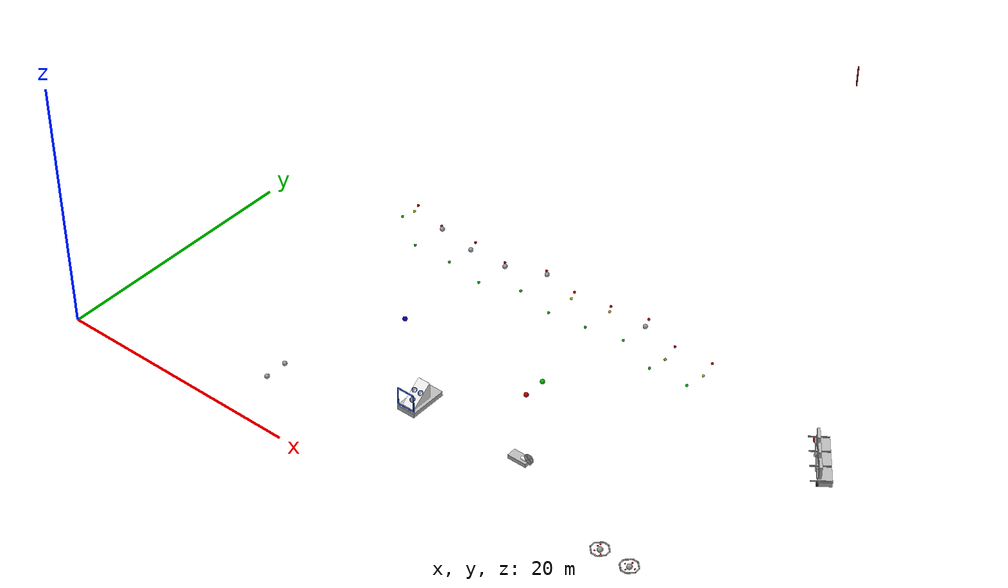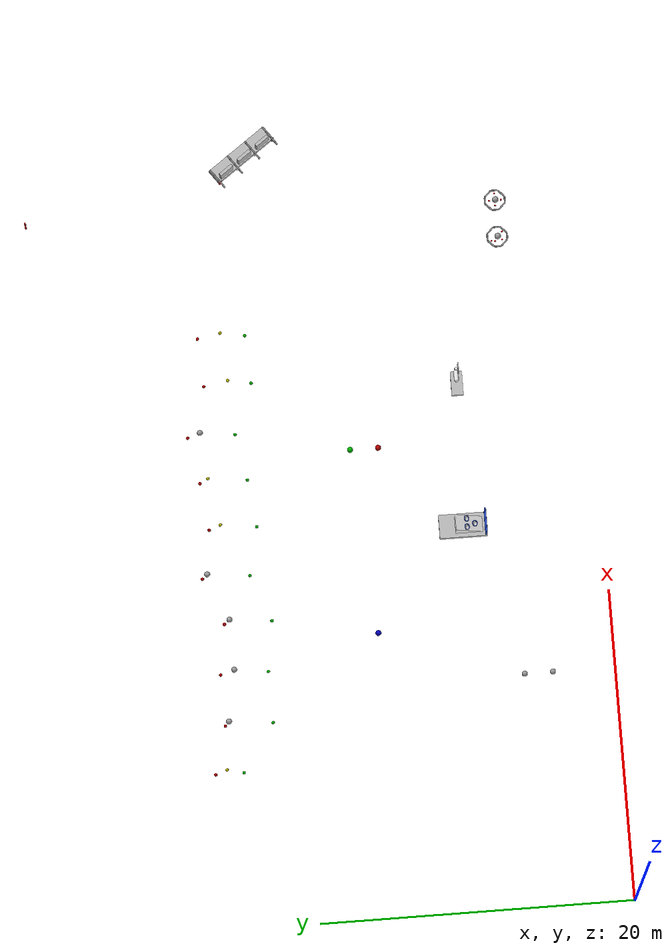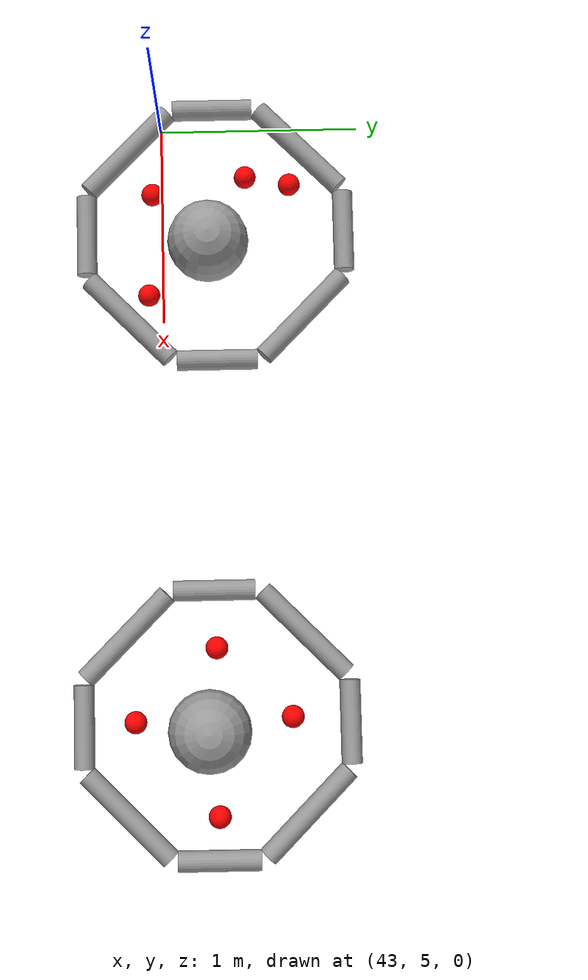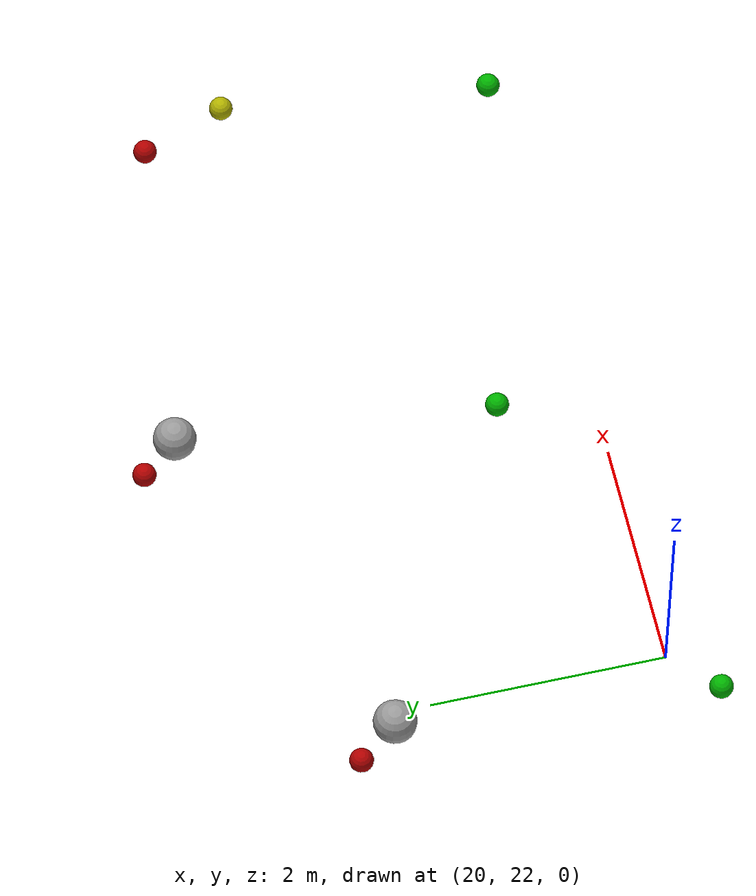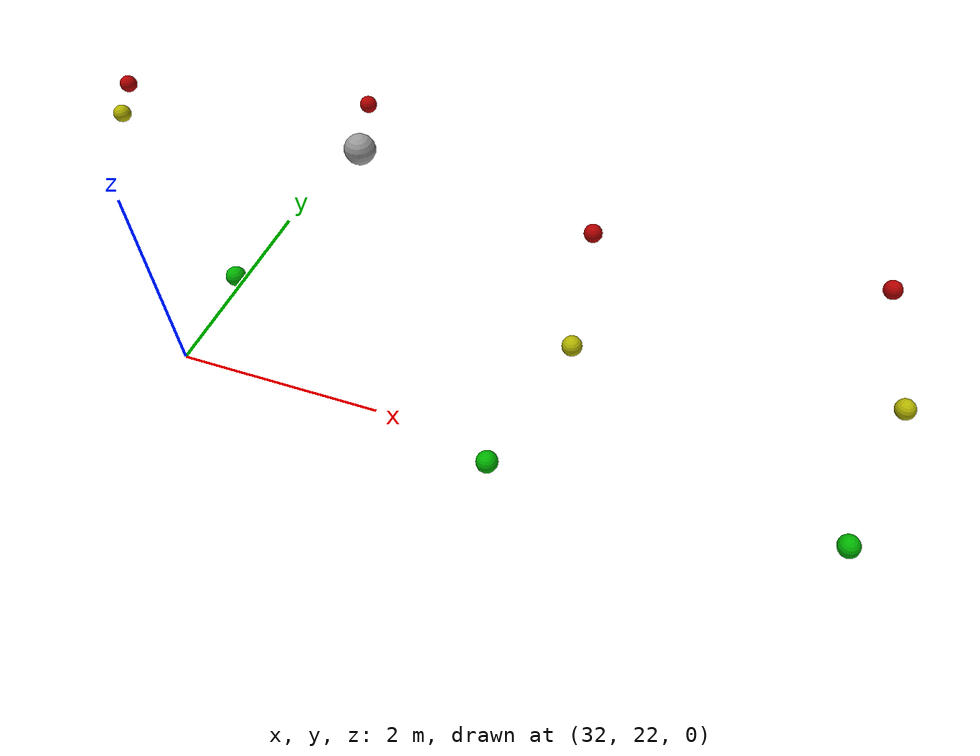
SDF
<sdf version="1.7">
 <world name="default">
  <light name="sun" type="directional">
   <pose>0 0 10 0 -0 0</pose>
   <diffuse>0.8 0.8 0.8 1</diffuse>
   <specular>0.2 0.2 0.2 1</specular>
   <attenuation>
    <range>1000</range>
    <constant>0.9</constant>
    <linear>0.01</linear>
    <quadratic>0.001</quadratic>
   </attenuation>
   <direction>-0.5 0.1 -0.9</direction>
   <spot><inner_angle>0</inner_angle><outer_angle>0</outer_angle><falloff>0</falloff></spot>
  </light>
  <gravity>0 0 -9.8</gravity>
  <magnetic_field>6e-06 2.3e-05 -4.2e-05</magnetic_field>
  <atmosphere type="adiabatic"/>
  <physics type="ode">
   <max_step_size>0.001</max_step_size>
   <real_time_factor>1</real_time_factor>
   <real_time_update_rate>1000</real_time_update_rate>
  </physics>
  <scene><ambient>0.4 0.4 0.4 1</ambient><background>0.7 0.7 0.7 1</background><shadows>1</shadows></scene>
  <spherical_coordinates>
   <surface_model>EARTH_WGS84</surface_model>
   <latitude_deg>0</latitude_deg>
   <longitude_deg>0</longitude_deg>
   <elevation>0</elevation>
   <heading_deg>0</heading_deg>
  </spherical_coordinates>
  <model name="Color Tutorial Model">
   <pose>50.6715 18.9177 0 0 0 -0.941851</pose>
   <static>1</static>
   <link name="red marker">
    <collision name="body_collision"><geometry><box><size>1 1 1</size></box></geometry></collision>
    <visual name="red marker">
     <geometry>
      <mesh><uri>model://task3_model/meshes/red_marker.stl</uri><scale>0.001 0.001 0.001</scale></mesh>
     </geometry>
     <material>
      <script><uri>file:///media/materials/scripts/gazebo.material</uri><name>Gazebo/Red</name></script>
     </material>
    </visual>
   </link>
   <link name="white markers">
    <collision name="body_collision"><geometry><box><size>1 1 1</size></box></geometry></collision>
    <visual name="white markers">
     <geometry>
      <mesh><uri>model://task3_model/meshes/white_markers.stl</uri><scale>0.001 0.001 0.001</scale></mesh>
     </geometry>
     <material>
      <script><uri>file:///media/materials/scripts/gazebo.material</uri><name>Gazebo/White</name></script>
     </material>
    </visual>
   </link>
   <link name="black marker">
    <collision name="body_collision"><geometry><box><size>1 1 1</size></box></geometry></collision>
    <visual name="black marker">
     <geometry>
      <mesh><uri>model://task3_model/meshes/black_marker.stl</uri><scale>0.001 0.001 0.001</scale></mesh>
     </geometry>
     <material>
      <script><uri>file:///media/materials/scripts/gazebo.material</uri><name>Gazebo/Black</name></script>
     </material>
    </visual>
   </link>
   <link name="base">
    <collision name="body_collision"><geometry><box><size>1 1 1</size></box></geometry></collision>
    <visual name="base">
     <geometry>
      <mesh><uri>model://task3_model/meshes/base.stl</uri><scale>0.001 0.001 0.001</scale></mesh>
     </geometry>
     <material>
      <script>
       <uri>model://task3_model/materials/scripts</uri>
       <uri>model://task3_model/materials/textures</uri>
       <name>DockBase/Image</name>
      </script>
     </material>
    </visual>
   </link>
   <link name="sticks">
    <collision name="body_collision"><geometry><box><size>1 1 1</size></box></geometry></collision>
    <visual name="sticks">
     <geometry>
      <mesh><uri>model://task3_model/meshes/sticks.stl</uri><scale>0.001 0.001 0.001</scale></mesh>
     </geometry>
     <material>
      <script><uri>file:///media/materials/scripts/gazebo.material</uri><name>Gazebo/Grey</name></script>
     </material>
    </visual>
   </link>
   <model name="dices">
    <pose>-3.8 0.7 0.9 0 -0 0</pose>
    <static>1</static>
    <link name="first dice">
     <collision name="body_collision"><geometry><box><size>1 0.2 1</size></box></geometry></collision>
     <visual name="first dice">
      <geometry><box><size>1 0.2 1</size></box></geometry>
      <material>
       <script>
        <uri>model://task3_model/materials/scripts</uri>
        <uri>model://task3_model/materials/textures</uri>
        <name>BlueDice/Image</name>
       </script>
      </material>
     </visual>
    </link>
    <link name="second dice">
     <pose>1.5 0 0 0 -0 0</pose>
     <collision name="body_collision"><geometry><box><size>1 0.2 1</size></box></geometry></collision>
     <visual name="second dice">
      <geometry><box><size>1 0.2 1</size></box></geometry>
      <material>
       <script>
        <uri>model://task3_model/materials/scripts</uri>
        <uri>model://task3_model/materials/textures</uri>
        <name>GreenDice/Image</name>
       </script>
      </material>
     </visual>
    </link>
    <link name="third dice">
     <pose>3 0 0 0 -0 0</pose>
     <collision name="body_collision"><geometry><box><size>1 0.2 1</size></box></geometry></collision>
     <visual name="third dice">
      <geometry><box><size>1 0.2 1</size></box></geometry>
      <material>
       <script>
        <uri>model://task3_model/materials/scripts</uri>
        <uri>model://task3_model/materials/textures</uri>
        <name>RedDice/Image</name>
       </script>
      </material>
     </visual>
    </link>
   </model>
  </model>
  <model name="task4">
   <model name="Gate buoy (red)">
    <pose>0 0 0.12065 0 -0 0</pose>
    <static>1</static>
    <link name="sphere">
     <inertial>
      <mass>1</mass>
      <inertia>
       <ixx>0.0135645</ixx>
       <ixy>0</ixy>
       <ixz>0</ixz>
       <iyy>0.0135645</iyy>
       <iyz>0</iyz>
       <izz>0.0135645</izz>
      </inertia>
     </inertial>
     <visual name="visual">
      <geometry><sphere><radius>0.18415</radius></sphere></geometry>
      <material>
       <lighting>1</lighting>
       <script><name>Gazebo/Grey</name><uri>file://media/materials/scripts/gazebo.material</uri></script>
       <shader type="pixel"><normal_map>__default__</normal_map></shader>
       <ambient>0.3 0.3 0.3 1</ambient>
       <diffuse>0.7 0 0 1</diffuse>
       <specular>0.01 0.01 0.01 1</specular>
       <emissive>0 0 0 1</emissive>
      </material>
     </visual>
     <collision name="collision">
      <geometry><sphere><radius>0.18415</radius></sphere></geometry>
      <surface>
       <friction>
        <ode><mu>1</mu><mu2>1</mu2><fdir1>0 0 0</fdir1><slip1>0</slip1><slip2>0</slip2></ode>
        <torsional>
         <coefficient>1</coefficient>
         <patch_radius>0</patch_radius>
         <surface_radius>0</surface_radius>
         <use_patch_radius>1</use_patch_radius>
         <ode><slip>0</slip></ode>
        </torsional>
       </friction>
       <bounce><restitution_coefficient>0</restitution_coefficient><threshold>1e+06</threshold></bounce>
       <contact>
        <collide_without_contact>0</collide_without_contact>
        <collide_without_contact_bitmask>1</collide_without_contact_bitmask>
        <collide_bitmask>1</collide_bitmask>
        <ode>
         <soft_cfm>0</soft_cfm>
         <soft_erp>0.2</soft_erp>
         <kp>1e+13</kp>
         <kd>1</kd>
         <max_vel>0.01</max_vel>
         <min_depth>0</min_depth>
        </ode>
        <bullet>
         <split_impulse>1</split_impulse>
         <split_impulse_penetration_threshold>-0.01</split_impulse_penetration_threshold>
         <soft_cfm>0</soft_cfm>
         <soft_erp>0.2</soft_erp>
         <kp>1e+13</kp>
         <kd>1</kd>
        </bullet>
       </contact>
      </surface>
     </collision>
    </link>
   </model>
   <model name="Gate buoy (green)">
    <pose>0 1.8 0.12065 0 -0 0</pose>
    <static>1</static>
    <link name="sphere">
     <inertial>
      <mass>1</mass>
      <inertia>
       <ixx>0.0135645</ixx>
       <ixy>0</ixy>
       <ixz>0</ixz>
       <iyy>0.0135645</iyy>
       <iyz>0</iyz>
       <izz>0.0135645</izz>
      </inertia>
     </inertial>
     <visual name="visual">
      <geometry><sphere><radius>0.18415</radius></sphere></geometry>
      <material>
       <lighting>1</lighting>
       <script><uri>file://media/materials/scripts/gazebo.material</uri><name>Gazebo/Grey</name></script>
       <shader type="pixel"><normal_map>__default__</normal_map></shader>
       <ambient>0.3 0.3 0.3 1</ambient>
       <diffuse>0 0.7 0 1</diffuse>
       <specular>0.01 0.01 0.01 1</specular>
       <emissive>0 0 0 1</emissive>
      </material>
     </visual>
     <collision name="collision">
      <geometry><sphere><radius>0.18415</radius></sphere></geometry>
      <surface>
       <friction>
        <ode><mu>1</mu><mu2>1</mu2><fdir1>0 0 0</fdir1><slip1>0</slip1><slip2>0</slip2></ode>
        <torsional>
         <coefficient>1</coefficient>
         <patch_radius>0</patch_radius>
         <surface_radius>0</surface_radius>
         <use_patch_radius>1</use_patch_radius>
         <ode><slip>0</slip></ode>
        </torsional>
       </friction>
       <bounce><restitution_coefficient>0</restitution_coefficient><threshold>1e+06</threshold></bounce>
       <contact>
        <collide_without_contact>0</collide_without_contact>
        <collide_without_contact_bitmask>1</collide_without_contact_bitmask>
        <collide_bitmask>1</collide_bitmask>
        <ode>
         <soft_cfm>0</soft_cfm>
         <soft_erp>0.2</soft_erp>
         <kp>1e+13</kp>
         <kd>1</kd>
         <max_vel>0.01</max_vel>
         <min_depth>0</min_depth>
        </ode>
        <bullet>
         <split_impulse>1</split_impulse>
         <split_impulse_penetration_threshold>-0.01</split_impulse_penetration_threshold>
         <soft_cfm>0</soft_cfm>
         <soft_erp>0.2</soft_erp>
         <kp>1e+13</kp>
         <kd>1</kd>
        </bullet>
       </contact>
      </surface>
     </collision>
    </link>
   </model>
   <model name="Gate buoy (blue)">
    <pose>-12 0.9 0.12065 0 -0 0</pose>
    <static>1</static>
    <link name="sphere">
     <inertial>
      <mass>1</mass>
      <inertia>
       <ixx>0.0135645</ixx>
       <ixy>0</ixy>
       <ixz>0</ixz>
       <iyy>0.0135645</iyy>
       <iyz>0</iyz>
       <izz>0.0135645</izz>
      </inertia>
     </inertial>
     <visual name="visual">
      <geometry><sphere><radius>0.18415</radius></sphere></geometry>
      <material>
       <lighting>1</lighting>
       <script><uri>file://media/materials/scripts/gazebo.material</uri><name>Gazebo/Grey</name></script>
       <shader type="pixel"><normal_map>__default__</normal_map></shader>
       <ambient>0.3 0.3 0.3 1</ambient>
       <diffuse>0 0 0.7 1</diffuse>
       <specular>0.01 0.01 0.01 1</specular>
       <emissive>0 0 0 1</emissive>
      </material>
     </visual>
     <collision name="collision">
      <geometry><sphere><radius>0.18415</radius></sphere></geometry>
      <surface>
       <friction>
        <ode><mu>1</mu><mu2>1</mu2><fdir1>0 0 0</fdir1><slip1>0</slip1><slip2>0</slip2></ode>
        <torsional>
         <coefficient>1</coefficient>
         <patch_radius>0</patch_radius>
         <surface_radius>0</surface_radius>
         <use_patch_radius>1</use_patch_radius>
         <ode><slip>0</slip></ode>
        </torsional>
       </friction>
       <bounce><restitution_coefficient>0</restitution_coefficient><threshold>1e+06</threshold></bounce>
       <contact>
        <collide_without_contact>0</collide_without_contact>
        <collide_without_contact_bitmask>1</collide_without_contact_bitmask>
        <collide_bitmask>1</collide_bitmask>
        <ode>
         <soft_cfm>0</soft_cfm>
         <soft_erp>0.2</soft_erp>
         <kp>1e+13</kp>
         <kd>1</kd>
         <max_vel>0.01</max_vel>
         <min_depth>0</min_depth>
        </ode>
        <bullet>
         <split_impulse>1</split_impulse>
         <split_impulse_penetration_threshold>-0.01</split_impulse_penetration_threshold>
         <soft_cfm>0</soft_cfm>
         <soft_erp>0.2</soft_erp>
         <kp>1e+13</kp>
         <kd>1</kd>
        </bullet>
       </contact>
      </surface>
     </collision>
    </link>
   </model>
   <pose>30.3179 14.0046 0 0 -0 0</pose>
  </model>
  <model name="Frame">
   <static>1</static>
   <pose>24.876 9.48322 -0.007552 1.57 -0 0</pose>
   <link name="Base">
    <collision name="body_collision"><geometry><box><size>1 1 1</size></box></geometry></collision>
    <visual name="base">
     <pose>0 0 0.5 0 -0 0</pose>
     <geometry>
      <mesh><uri>model://task6_model/meshes/Czesc1_do_wiaderek.stl</uri><scale>0.001 0.001 0.001</scale></mesh>
     </geometry>
     <material>
      <script>
       <uri>model://task6_model/materials/scripts</uri>
       <uri>model://task6_model/materials/textures</uri>
       <name>DockBase/Image</name>
      </script>
     </material>
    </visual>
   </link>
   <link name="Frame">
    <pose>0 1 1.5 0 -0 0</pose>
    <collision name="body_collision"><geometry><box><size>1 1 1</size></box></geometry></collision>
    <visual name="frame">
     <pose>0 0 0.5 0 -0 0</pose>
     <geometry>
      <mesh><uri>model://task6_model/meshes/Czesc2_do_wiaderek.stl</uri><scale>0.001 0.001 0.001</scale></mesh>
     </geometry>
     <material>
      <script><uri>file://media/materials/scripts/gazebo.material</uri><name>Gazebo/Blue</name></script>
     </material>
    </visual>
   </link>
   <link name="Main Box">
    <pose>0 0 0 0 -1.57 0</pose>
    <collision name="body_collision"><geometry><box><size>1 1 1</size></box></geometry></collision>
    <visual name="main_box">
     <pose>0 0 0.5 0 -0 0</pose>
     <geometry>
      <mesh><uri>model://task6_model/meshes/Czesc3_wiaderka.stl</uri><scale>0.0001 0.0001 0.0001</scale></mesh>
     </geometry>
     <material>
      <script><uri>file://media/materials/scripts/gazebo.material</uri><name>Gazebo/White</name></script>
     </material>
    </visual>
   </link>
   <link name="Buckets">
    <pose>0 0 0 0 -1.57 0</pose>
    <collision name="body_collision"><geometry><box><size>1 1 1</size></box></geometry></collision>
    <visual name="buckets">
     <pose>0 0 0.5 0 -0 0</pose>
     <geometry>
      <mesh><uri>model://task6_model/meshes/Czesc4_wiaderkav1.stl</uri><scale>1e-05 1e-05 1e-05</scale></mesh>
     </geometry>
     <material>
      <script><uri>file://media/materials/scripts/gazebo.material</uri><name>Gazebo/Blue</name></script>
     </material>
    </visual>
   </link>
  </model>
  <model name="task8">
   <model name="Gate buoy (black) #1">
    <pose>0 0 0.12065 0 -0 0</pose>
    <static>1</static>
    <link name="sphere">
     <inertial>
      <mass>1</mass>
      <inertia>
       <ixx>0.0135645</ixx>
       <ixy>0</ixy>
       <ixz>0</ixz>
       <iyy>0.0135645</iyy>
       <iyz>0</iyz>
       <izz>0.0135645</izz>
      </inertia>
     </inertial>
     <visual name="visual">
      <geometry><sphere><radius>0.18415</radius></sphere></geometry>
      <material>
       <lighting>1</lighting>
       <script><uri>file://media/materials/scripts/gazebo.material</uri><name>Gazebo/Grey</name></script>
       <shader type="pixel"><normal_map>__default__</normal_map></shader>
       <ambient>0.3 0.3 0.3 1</ambient>
       <diffuse>0 0 0 1</diffuse>
       <specular>0.01 0.01 0.01 1</specular>
       <emissive>0 0 0 1</emissive>
      </material>
     </visual>
     <collision name="collision">
      <geometry><sphere><radius>0.18415</radius></sphere></geometry>
      <surface>
       <friction>
        <ode><mu>1</mu><mu2>1</mu2><fdir1>0 0 0</fdir1><slip1>0</slip1><slip2>0</slip2></ode>
        <torsional>
         <coefficient>1</coefficient>
         <patch_radius>0</patch_radius>
         <surface_radius>0</surface_radius>
         <use_patch_radius>1</use_patch_radius>
         <ode><slip>0</slip></ode>
        </torsional>
       </friction>
       <bounce><restitution_coefficient>0</restitution_coefficient><threshold>1e+06</threshold></bounce>
       <contact>
        <collide_without_contact>0</collide_without_contact>
        <collide_without_contact_bitmask>1</collide_without_contact_bitmask>
        <collide_bitmask>1</collide_bitmask>
        <ode>
         <soft_cfm>0</soft_cfm>
         <soft_erp>0.2</soft_erp>
         <kp>1e+13</kp>
         <kd>1</kd>
         <max_vel>0.01</max_vel>
         <min_depth>0</min_depth>
        </ode>
        <bullet>
         <split_impulse>1</split_impulse>
         <split_impulse_penetration_threshold>-0.01</split_impulse_penetration_threshold>
         <soft_cfm>0</soft_cfm>
         <soft_erp>0.2</soft_erp>
         <kp>1e+13</kp>
         <kd>1</kd>
        </bullet>
       </contact>
      </surface>
     </collision>
    </link>
   </model>
   <model name="Gate buoy (black) #2">
    <pose>0 1.8 0.12065 0 -0 0</pose>
    <static>1</static>
    <link name="sphere">
     <inertial>
      <mass>1</mass>
      <inertia>
       <ixx>0.0135645</ixx>
       <ixy>0</ixy>
       <ixz>0</ixz>
       <iyy>0.0135645</iyy>
       <iyz>0</iyz>
       <izz>0.0135645</izz>
      </inertia>
     </inertial>
     <visual name="visual">
      <geometry><sphere><radius>0.18415</radius></sphere></geometry>
      <material>
       <lighting>1</lighting>
       <script><uri>file://media/materials/scripts/gazebo.material</uri><name>Gazebo/Grey</name></script>
       <shader type="pixel"><normal_map>__default__</normal_map></shader>
       <ambient>0.3 0.3 0.3 1</ambient>
       <diffuse>0 0 0 1</diffuse>
       <specular>0.01 0.01 0.01 1</specular>
       <emissive>0 0 0 1</emissive>
      </material>
     </visual>
     <collision name="collision">
      <geometry><sphere><radius>0.18415</radius></sphere></geometry>
      <surface>
       <friction>
        <ode><mu>1</mu><mu2>1</mu2><fdir1>0 0 0</fdir1><slip1>0</slip1><slip2>0</slip2></ode>
        <torsional>
         <coefficient>1</coefficient>
         <patch_radius>0</patch_radius>
         <surface_radius>0</surface_radius>
         <use_patch_radius>1</use_patch_radius>
         <ode><slip>0</slip></ode>
        </torsional>
       </friction>
       <bounce><restitution_coefficient>0</restitution_coefficient><threshold>1e+06</threshold></bounce>
       <contact>
        <collide_without_contact>0</collide_without_contact>
        <collide_without_contact_bitmask>1</collide_without_contact_bitmask>
        <collide_bitmask>1</collide_bitmask>
        <ode>
         <soft_cfm>0</soft_cfm>
         <soft_erp>0.2</soft_erp>
         <kp>1e+13</kp>
         <kd>1</kd>
         <max_vel>0.01</max_vel>
         <min_depth>0</min_depth>
        </ode>
        <bullet>
         <split_impulse>1</split_impulse>
         <split_impulse_penetration_threshold>-0.01</split_impulse_penetration_threshold>
         <soft_cfm>0</soft_cfm>
         <soft_erp>0.2</soft_erp>
         <kp>1e+13</kp>
         <kd>1</kd>
        </bullet>
       </contact>
      </surface>
     </collision>
    </link>
   </model>
   <pose>15 4 0 0 -0 0</pose>
  </model>
  <model name="Task7_model">
   <static>1</static>
   <pose>34.2162 8.64624 0 1.57 -0 1.57</pose>
   <link name="Base">
    <pose>0 0 0 -1.57 0 0</pose>
    <collision name="body_collision"><geometry><box><size>1 1 1</size></box></geometry></collision>
    <visual name="base">
     <geometry>
      <mesh>
       <uri>model://task7_model/meshes/SeaSentinel_TASK7_base.stl</uri>
       <scale>0.0001 0.0001 0.0001</scale>
      </mesh>
     </geometry>
     <material>
      <script>
       <uri>model://task7_model/materials/scripts</uri>
       <uri>model://task7_model/materials/textures</uri>
       <name>DockBase/Image</name>
      </script>
     </material>
    </visual>
   </link>
   <link name="Pipes">
    <pose>0 0 0 -1.57 0 0</pose>
    <collision name="body_collision"><geometry><box><size>1 1 1</size></box></geometry></collision>
    <visual name="Pipes">
     <geometry>
      <mesh>
       <uri>model://task7_model/meshes/SeaSentinel_TASK7_rest.stl</uri>
       <scale>0.0001 0.0001 0.0001</scale>
      </mesh>
     </geometry>
     <material>
      <script><uri>file://media/materials/scripts/gazebo.material</uri><name>Gazebo/White</name></script>
     </material>
    </visual>
   </link>
   <model name="Target">
    <static>1</static>
    <pose>-0.05 -0.07 0 0 -0 0</pose>
    <link name="target base">
     <pose>-0.1 0.8 0.8 0 1.57 0</pose>
     <collision name="body_collision">
      <geometry><cylinder><length>0.05</length><radius>0.381</radius></cylinder></geometry>
     </collision>
     <visual name="target base">
      <geometry><cylinder><length>0.05</length><radius>0.381</radius></cylinder></geometry>
      <material>
       <script>
        <uri>model://task7_model/materials/scripts</uri>
        <uri>model://task7_model/materials/textures</uri>
        <name>Target/Image</name>
       </script>
      </material>
     </visual>
    </link>
    <link name="Target whole">
     <pose>-0.1 0.8 0.8 0 1.57 0</pose>
     <collision name="body_collision">
      <geometry><cylinder><length>0.06</length><radius>0.075</radius></cylinder></geometry>
     </collision>
     <visual name="target whole">
      <geometry><cylinder><length>0.06</length><radius>0.075</radius></cylinder></geometry>
      <material>
       <script><uri>file://media/materials/scripts/gazebo.material</uri><name>Gazebo/White</name></script>
      </material>
     </visual>
    </link>
    <link name="Target Stripe">
     <pose>-0.1 0.8 0.8 0.785 -0 0</pose>
     <collision name="body_collision"><geometry><box><size>0.06 0.76 0.06</size></box></geometry></collision>
     <visual name="target stripe">
      <geometry><box><size>0.06 0.76 0.06</size></box></geometry>
      <material>
       <script><uri>file://media/materials/scripts/gazebo.material</uri><name>Gazebo/White</name></script>
      </material>
     </visual>
    </link>
    <link name="Target stripe 2">
     <pose>-0.1 0.8 0.8 -0.785 0 0</pose>
     <collision name="body_collision"><geometry><box><size>0.06 0.76 0.06</size></box></geometry></collision>
     <visual name="target stripe 2">
      <geometry><box><size>0.06 0.76 0.06</size></box></geometry>
      <material>
       <script><uri>file://media/materials/scripts/gazebo.material</uri><name>Gazebo/White</name></script>
      </material>
     </visual>
    </link>
   </model>
  </model>
  <model name="task2">
   <model name="Small gate buoy (red) #1">
    <pose>-0.730062 0 0 0 -0 0</pose>
    <static>1</static>
    <link name="sphere">
     <inertial>
      <mass>1</mass>
      <inertia><ixx>0.06773</ixx><ixy>0</ixy><ixz>0</ixz><iyy>0.06773</iyy><iyz>0</iyz><izz>0.06773</izz></inertia>
     </inertial>
     <visual name="visual">
      <geometry><sphere><radius>0.1016</radius></sphere></geometry>
      <material>
       <lighting>1</lighting>
       <script><uri>file://media/materials/scripts/gazebo.material</uri><name>Gazebo/Grey</name></script>
       <shader type="pixel"><normal_map>__default__</normal_map></shader>
       <ambient>0.3 0.3 0.3 1</ambient>
       <diffuse>0.7 0 0 1</diffuse>
       <specular>0.01 0.01 0.01 1</specular>
       <emissive>0 0 0 1</emissive>
      </material>
     </visual>
     <collision name="collision">
      <geometry><sphere><radius>0.1016</radius></sphere></geometry>
      <surface>
       <friction>
        <ode><mu>1</mu><mu2>1</mu2><fdir1>0 0 0</fdir1><slip1>0</slip1><slip2>0</slip2></ode>
        <torsional>
         <coefficient>1</coefficient>
         <patch_radius>0</patch_radius>
         <surface_radius>0</surface_radius>
         <use_patch_radius>1</use_patch_radius>
         <ode><slip>0</slip></ode>
        </torsional>
       </friction>
       <bounce><restitution_coefficient>0</restitution_coefficient><threshold>1e+06</threshold></bounce>
       <contact>
        <collide_without_contact>0</collide_without_contact>
        <collide_without_contact_bitmask>1</collide_without_contact_bitmask>
        <collide_bitmask>1</collide_bitmask>
        <ode>
         <soft_cfm>0</soft_cfm>
         <soft_erp>0.2</soft_erp>
         <kp>1e+13</kp>
         <kd>1</kd>
         <max_vel>0.01</max_vel>
         <min_depth>0</min_depth>
        </ode>
        <bullet>
         <split_impulse>1</split_impulse>
         <split_impulse_penetration_threshold>-0.01</split_impulse_penetration_threshold>
         <soft_cfm>0</soft_cfm>
         <soft_erp>0.2</soft_erp>
         <kp>1e+13</kp>
         <kd>1</kd>
        </bullet>
       </contact>
      </surface>
     </collision>
    </link>
   </model>
   <model name="Small gate buoy (green) #1">
    <pose>1.06994 0 0 0 -0 0</pose>
    <static>1</static>
    <link name="sphere">
     <inertial>
      <mass>1</mass>
      <inertia><ixx>0.06773</ixx><ixy>0</ixy><ixz>0</ixz><iyy>0.06773</iyy><iyz>0</iyz><izz>0.06773</izz></inertia>
     </inertial>
     <visual name="visual">
      <geometry><sphere><radius>0.1016</radius></sphere></geometry>
      <material>
       <lighting>1</lighting>
       <script><uri>file://media/materials/scripts/gazebo.material</uri><name>Gazebo/Grey</name></script>
       <shader type="pixel"><normal_map>__default__</normal_map></shader>
       <ambient>0.3 0.3 0.3 1</ambient>
       <diffuse>0 0.7 0 1</diffuse>
       <specular>0.01 0.01 0.01 1</specular>
       <emissive>0 0 0 1</emissive>
      </material>
     </visual>
     <collision name="collision">
      <geometry><sphere><radius>0.1016</radius></sphere></geometry>
      <surface>
       <friction>
        <ode><mu>1</mu><mu2>1</mu2><fdir1>0 0 0</fdir1><slip1>0</slip1><slip2>0</slip2></ode>
        <torsional>
         <coefficient>1</coefficient>
         <patch_radius>0</patch_radius>
         <surface_radius>0</surface_radius>
         <use_patch_radius>1</use_patch_radius>
         <ode><slip>0</slip></ode>
        </torsional>
       </friction>
       <bounce><restitution_coefficient>0</restitution_coefficient><threshold>1e+06</threshold></bounce>
       <contact>
        <collide_without_contact>0</collide_without_contact>
        <collide_without_contact_bitmask>1</collide_without_contact_bitmask>
        <collide_bitmask>1</collide_bitmask>
        <ode>
         <soft_cfm>0</soft_cfm>
         <soft_erp>0.2</soft_erp>
         <kp>1e+13</kp>
         <kd>1</kd>
         <max_vel>0.01</max_vel>
         <min_depth>0</min_depth>
        </ode>
        <bullet>
         <split_impulse>1</split_impulse>
         <split_impulse_penetration_threshold>-0.01</split_impulse_penetration_threshold>
         <soft_cfm>0</soft_cfm>
         <soft_erp>0.2</soft_erp>
         <kp>1e+13</kp>
         <kd>1</kd>
        </bullet>
       </contact>
      </surface>
     </collision>
    </link>
   </model>
   <model name="Small gate buoy (yellow) #1">
    <pose>0.011013 0.263625 0 0 -0 0</pose>
    <static>1</static>
    <link name="sphere">
     <inertial>
      <mass>1</mass>
      <inertia><ixx>0.06773</ixx><ixy>0</ixy><ixz>0</ixz><iyy>0.06773</iyy><iyz>0</iyz><izz>0.06773</izz></inertia>
     </inertial>
     <visual name="visual">
      <geometry><sphere><radius>0.1016</radius></sphere></geometry>
      <material>
       <lighting>1</lighting>
       <script><name>Gazebo/Grey</name><uri>file://media/materials/scripts/gazebo.material</uri></script>
       <shader type="pixel"><normal_map>__default__</normal_map></shader>
       <ambient>0.3 0.3 0.3 1</ambient>
       <diffuse>0.7 0.7 0 1</diffuse>
       <specular>0.01 0.01 0.01 1</specular>
       <emissive>0 0 0 1</emissive>
      </material>
     </visual>
     <collision name="collision">
      <geometry><sphere><radius>0.1016</radius></sphere></geometry>
      <surface>
       <friction>
        <ode><mu>1</mu><mu2>1</mu2><fdir1>0 0 0</fdir1><slip1>0</slip1><slip2>0</slip2></ode>
        <torsional>
         <coefficient>1</coefficient>
         <patch_radius>0</patch_radius>
         <surface_radius>0</surface_radius>
         <use_patch_radius>1</use_patch_radius>
         <ode><slip>0</slip></ode>
        </torsional>
       </friction>
       <bounce><restitution_coefficient>0</restitution_coefficient><threshold>1e+06</threshold></bounce>
       <contact>
        <collide_without_contact>0</collide_without_contact>
        <collide_without_contact_bitmask>1</collide_without_contact_bitmask>
        <collide_bitmask>1</collide_bitmask>
        <ode>
         <soft_cfm>0</soft_cfm>
         <soft_erp>0.2</soft_erp>
         <kp>1e+13</kp>
         <kd>1</kd>
         <max_vel>0.01</max_vel>
         <min_depth>0</min_depth>
        </ode>
        <bullet>
         <split_impulse>1</split_impulse>
         <split_impulse_penetration_threshold>-0.01</split_impulse_penetration_threshold>
         <soft_cfm>0</soft_cfm>
         <soft_erp>0.2</soft_erp>
         <kp>1e+13</kp>
         <kd>1</kd>
        </bullet>
       </contact>
      </surface>
     </collision>
    </link>
   </model>
   <model name="Small gate buoy (red) #2">
    <pose>0.107222 3.07455 0 0 -0 0</pose>
    <static>1</static>
    <link name="sphere">
     <inertial>
      <mass>1</mass>
      <inertia><ixx>0.06773</ixx><ixy>0</ixy><ixz>0</ixz><iyy>0.06773</iyy><iyz>0</iyz><izz>0.06773</izz></inertia>
     </inertial>
     <visual name="visual">
      <geometry><sphere><radius>0.1016</radius></sphere></geometry>
      <material>
       <lighting>1</lighting>
       <script><uri>file://media/materials/scripts/gazebo.material</uri><name>Gazebo/Grey</name></script>
       <shader type="pixel"><normal_map>__default__</normal_map></shader>
       <ambient>0.3 0.3 0.3 1</ambient>
       <diffuse>0.7 0 0 1</diffuse>
       <specular>0.01 0.01 0.01 1</specular>
       <emissive>0 0 0 1</emissive>
      </material>
     </visual>
     <collision name="collision">
      <geometry><sphere><radius>0.1016</radius></sphere></geometry>
      <surface>
       <friction>
        <ode><mu>1</mu><mu2>1</mu2><fdir1>0 0 0</fdir1><slip1>0</slip1><slip2>0</slip2></ode>
        <torsional>
         <coefficient>1</coefficient>
         <patch_radius>0</patch_radius>
         <surface_radius>0</surface_radius>
         <use_patch_radius>1</use_patch_radius>
         <ode><slip>0</slip></ode>
        </torsional>
       </friction>
       <bounce><restitution_coefficient>0</restitution_coefficient><threshold>1e+06</threshold></bounce>
       <contact>
        <collide_without_contact>0</collide_without_contact>
        <collide_without_contact_bitmask>1</collide_without_contact_bitmask>
        <collide_bitmask>1</collide_bitmask>
        <ode>
         <soft_cfm>0</soft_cfm>
         <soft_erp>0.2</soft_erp>
         <kp>1e+13</kp>
         <kd>1</kd>
         <max_vel>0.01</max_vel>
         <min_depth>0</min_depth>
        </ode>
        <bullet>
         <split_impulse>1</split_impulse>
         <split_impulse_penetration_threshold>-0.01</split_impulse_penetration_threshold>
         <soft_cfm>0</soft_cfm>
         <soft_erp>0.2</soft_erp>
         <kp>1e+13</kp>
         <kd>1</kd>
        </bullet>
       </contact>
      </surface>
     </collision>
    </link>
   </model>
   <model name="Small gate buoy (green) #2">
    <pose>3.15522 3.07455 0 0 -0 0</pose>
    <static>1</static>
    <link name="sphere">
     <inertial>
      <mass>1</mass>
      <inertia><ixx>0.06773</ixx><ixy>0</ixy><ixz>0</ixz><iyy>0.06773</iyy><iyz>0</iyz><izz>0.06773</izz></inertia>
     </inertial>
     <visual name="visual">
      <geometry><sphere><radius>0.1016</radius></sphere></geometry>
      <material>
       <lighting>1</lighting>
       <script><uri>file://media/materials/scripts/gazebo.material</uri><name>Gazebo/Grey</name></script>
       <shader type="pixel"><normal_map>__default__</normal_map></shader>
       <ambient>0.3 0.3 0.3 1</ambient>
       <diffuse>0 0.7 0 1</diffuse>
       <specular>0.01 0.01 0.01 1</specular>
       <emissive>0 0 0 1</emissive>
      </material>
     </visual>
     <collision name="collision">
      <geometry><sphere><radius>0.1016</radius></sphere></geometry>
      <surface>
       <friction>
        <ode><mu>1</mu><mu2>1</mu2><fdir1>0 0 0</fdir1><slip1>0</slip1><slip2>0</slip2></ode>
        <torsional>
         <coefficient>1</coefficient>
         <patch_radius>0</patch_radius>
         <surface_radius>0</surface_radius>
         <use_patch_radius>1</use_patch_radius>
         <ode><slip>0</slip></ode>
        </torsional>
       </friction>
       <bounce><restitution_coefficient>0</restitution_coefficient><threshold>1e+06</threshold></bounce>
       <contact>
        <collide_without_contact>0</collide_without_contact>
        <collide_without_contact_bitmask>1</collide_without_contact_bitmask>
        <collide_bitmask>1</collide_bitmask>
        <ode>
         <soft_cfm>0</soft_cfm>
         <soft_erp>0.2</soft_erp>
         <kp>1e+13</kp>
         <kd>1</kd>
         <max_vel>0.01</max_vel>
         <min_depth>0</min_depth>
        </ode>
        <bullet>
         <split_impulse>1</split_impulse>
         <split_impulse_penetration_threshold>-0.01</split_impulse_penetration_threshold>
         <soft_cfm>0</soft_cfm>
         <soft_erp>0.2</soft_erp>
         <kp>1e+13</kp>
         <kd>1</kd>
        </bullet>
       </contact>
      </surface>
     </collision>
    </link>
   </model>
   <model name="Gate buoy (black) #2">
    <pose>0.362765 3.36006 0 0 -0 0</pose>
    <static>1</static>
    <link name="sphere">
     <inertial>
      <mass>1</mass>
      <inertia>
       <ixx>0.0135645</ixx>
       <ixy>0</ixy>
       <ixz>0</ixz>
       <iyy>0.0135645</iyy>
       <iyz>0</iyz>
       <izz>0.0135645</izz>
      </inertia>
     </inertial>
     <visual name="visual">
      <geometry><sphere><radius>0.18415</radius></sphere></geometry>
      <material>
       <lighting>1</lighting>
       <script><uri>file://media/materials/scripts/gazebo.material</uri><name>Gazebo/Grey</name></script>
       <shader type="pixel"><normal_map>__default__</normal_map></shader>
       <ambient>0.3 0.3 0.3 1</ambient>
       <diffuse>0 0 0 1</diffuse>
       <specular>0.01 0.01 0.01 1</specular>
       <emissive>0 0 0 1</emissive>
      </material>
     </visual>
     <collision name="collision">
      <geometry><sphere><radius>0.18415</radius></sphere></geometry>
      <surface>
       <friction>
        <ode><mu>1</mu><mu2>1</mu2><fdir1>0 0 0</fdir1><slip1>0</slip1><slip2>0</slip2></ode>
        <torsional>
         <coefficient>1</coefficient>
         <patch_radius>0</patch_radius>
         <surface_radius>0</surface_radius>
         <use_patch_radius>1</use_patch_radius>
         <ode><slip>0</slip></ode>
        </torsional>
       </friction>
       <bounce><restitution_coefficient>0</restitution_coefficient><threshold>1e+06</threshold></bounce>
       <contact>
        <collide_without_contact>0</collide_without_contact>
        <collide_without_contact_bitmask>1</collide_without_contact_bitmask>
        <collide_bitmask>1</collide_bitmask>
        <ode>
         <soft_cfm>0</soft_cfm>
         <soft_erp>0.2</soft_erp>
         <kp>1e+13</kp>
         <kd>1</kd>
         <max_vel>0.01</max_vel>
         <min_depth>0</min_depth>
        </ode>
        <bullet>
         <split_impulse>1</split_impulse>
         <split_impulse_penetration_threshold>-0.01</split_impulse_penetration_threshold>
         <soft_cfm>0</soft_cfm>
         <soft_erp>0.2</soft_erp>
         <kp>1e+13</kp>
         <kd>1</kd>
        </bullet>
       </contact>
      </surface>
     </collision>
    </link>
   </model>
   <model name="Small gate buoy (red) #3">
    <pose>0.048114 6.3805 0 0 -0 0</pose>
    <static>1</static>
    <link name="sphere">
     <inertial>
      <mass>1</mass>
      <inertia><ixx>0.06773</ixx><ixy>0</ixy><ixz>0</ixz><iyy>0.06773</iyy><iyz>0</iyz><izz>0.06773</izz></inertia>
     </inertial>
     <visual name="visual">
      <geometry><sphere><radius>0.1016</radius></sphere></geometry>
      <material>
       <lighting>1</lighting>
       <script><uri>file://media/materials/scripts/gazebo.material</uri><name>Gazebo/Grey</name></script>
       <shader type="pixel"><normal_map>__default__</normal_map></shader>
       <ambient>0.3 0.3 0.3 1</ambient>
       <diffuse>0.7 0 0 1</diffuse>
       <specular>0.01 0.01 0.01 1</specular>
       <emissive>0 0 0 1</emissive>
      </material>
     </visual>
     <collision name="collision">
      <geometry><sphere><radius>0.1016</radius></sphere></geometry>
      <surface>
       <friction>
        <ode><mu>1</mu><mu2>1</mu2><fdir1>0 0 0</fdir1><slip1>0</slip1><slip2>0</slip2></ode>
        <torsional>
         <coefficient>1</coefficient>
         <patch_radius>0</patch_radius>
         <surface_radius>0</surface_radius>
         <use_patch_radius>1</use_patch_radius>
         <ode><slip>0</slip></ode>
        </torsional>
       </friction>
       <bounce><restitution_coefficient>0</restitution_coefficient><threshold>1e+06</threshold></bounce>
       <contact>
        <collide_without_contact>0</collide_without_contact>
        <collide_without_contact_bitmask>1</collide_without_contact_bitmask>
        <collide_bitmask>1</collide_bitmask>
        <ode>
         <soft_cfm>0</soft_cfm>
         <soft_erp>0.2</soft_erp>
         <kp>1e+13</kp>
         <kd>1</kd>
         <max_vel>0.01</max_vel>
         <min_depth>0</min_depth>
        </ode>
        <bullet>
         <split_impulse>1</split_impulse>
         <split_impulse_penetration_threshold>-0.01</split_impulse_penetration_threshold>
         <soft_cfm>0</soft_cfm>
         <soft_erp>0.2</soft_erp>
         <kp>1e+13</kp>
         <kd>1</kd>
        </bullet>
       </contact>
      </surface>
     </collision>
    </link>
   </model>
   <model name="Small gate buoy (green) #3">
    <pose>3.09611 6.3805 0 0 -0 0</pose>
    <static>1</static>
    <link name="sphere">
     <inertial>
      <mass>1</mass>
      <inertia><ixx>0.06773</ixx><ixy>0</ixy><ixz>0</ixz><iyy>0.06773</iyy><iyz>0</iyz><izz>0.06773</izz></inertia>
     </inertial>
     <visual name="visual">
      <geometry><sphere><radius>0.1016</radius></sphere></geometry>
      <material>
       <lighting>1</lighting>
       <script><uri>file://media/materials/scripts/gazebo.material</uri><name>Gazebo/Grey</name></script>
       <shader type="pixel"><normal_map>__default__</normal_map></shader>
       <ambient>0.3 0.3 0.3 1</ambient>
       <diffuse>0 0.7 0 1</diffuse>
       <specular>0.01 0.01 0.01 1</specular>
       <emissive>0 0 0 1</emissive>
      </material>
     </visual>
     <collision name="collision">
      <geometry><sphere><radius>0.1016</radius></sphere></geometry>
      <surface>
       <friction>
        <ode><mu>1</mu><mu2>1</mu2><fdir1>0 0 0</fdir1><slip1>0</slip1><slip2>0</slip2></ode>
        <torsional>
         <coefficient>1</coefficient>
         <patch_radius>0</patch_radius>
         <surface_radius>0</surface_radius>
         <use_patch_radius>1</use_patch_radius>
         <ode><slip>0</slip></ode>
        </torsional>
       </friction>
       <bounce><restitution_coefficient>0</restitution_coefficient><threshold>1e+06</threshold></bounce>
       <contact>
        <collide_without_contact>0</collide_without_contact>
        <collide_without_contact_bitmask>1</collide_without_contact_bitmask>
        <collide_bitmask>1</collide_bitmask>
        <ode>
         <soft_cfm>0</soft_cfm>
         <soft_erp>0.2</soft_erp>
         <kp>1e+13</kp>
         <kd>1</kd>
         <max_vel>0.01</max_vel>
         <min_depth>0</min_depth>
        </ode>
        <bullet>
         <split_impulse>1</split_impulse>
         <split_impulse_penetration_threshold>-0.01</split_impulse_penetration_threshold>
         <soft_cfm>0</soft_cfm>
         <soft_erp>0.2</soft_erp>
         <kp>1e+13</kp>
         <kd>1</kd>
        </bullet>
       </contact>
      </surface>
     </collision>
    </link>
   </model>
   <model name="Gate buoy (black) #3">
    <pose>0.939068 6.66601 0 0 -0 0</pose>
    <static>1</static>
    <link name="sphere">
     <inertial>
      <mass>1</mass>
      <inertia>
       <ixx>0.0135645</ixx>
       <ixy>0</ixy>
       <ixz>0</ixz>
       <iyy>0.0135645</iyy>
       <iyz>0</iyz>
       <izz>0.0135645</izz>
      </inertia>
     </inertial>
     <visual name="visual">
      <geometry><sphere><radius>0.18415</radius></sphere></geometry>
      <material>
       <lighting>1</lighting>
       <script><uri>file://media/materials/scripts/gazebo.material</uri><name>Gazebo/Grey</name></script>
       <shader type="pixel"><normal_map>__default__</normal_map></shader>
       <ambient>0.3 0.3 0.3 1</ambient>
       <diffuse>0 0 0 1</diffuse>
       <specular>0.01 0.01 0.01 1</specular>
       <emissive>0 0 0 1</emissive>
      </material>
     </visual>
     <collision name="collision">
      <geometry><sphere><radius>0.18415</radius></sphere></geometry>
      <surface>
       <friction>
        <ode><mu>1</mu><mu2>1</mu2><fdir1>0 0 0</fdir1><slip1>0</slip1><slip2>0</slip2></ode>
        <torsional>
         <coefficient>1</coefficient>
         <patch_radius>0</patch_radius>
         <surface_radius>0</surface_radius>
         <use_patch_radius>1</use_patch_radius>
         <ode><slip>0</slip></ode>
        </torsional>
       </friction>
       <bounce><restitution_coefficient>0</restitution_coefficient><threshold>1e+06</threshold></bounce>
       <contact>
        <collide_without_contact>0</collide_without_contact>
        <collide_without_contact_bitmask>1</collide_without_contact_bitmask>
        <collide_bitmask>1</collide_bitmask>
        <ode>
         <soft_cfm>0</soft_cfm>
         <soft_erp>0.2</soft_erp>
         <kp>1e+13</kp>
         <kd>1</kd>
         <max_vel>0.01</max_vel>
         <min_depth>0</min_depth>
        </ode>
        <bullet>
         <split_impulse>1</split_impulse>
         <split_impulse_penetration_threshold>-0.01</split_impulse_penetration_threshold>
         <soft_cfm>0</soft_cfm>
         <soft_erp>0.2</soft_erp>
         <kp>1e+13</kp>
         <kd>1</kd>
        </bullet>
       </contact>
      </surface>
     </collision>
    </link>
   </model>
   <model name="Small gate buoy (red) #4">
    <pose>0.525677 9.62981 0 0 -0 0</pose>
    <static>1</static>
    <link name="sphere">
     <inertial>
      <mass>1</mass>
      <inertia><ixx>0.06773</ixx><ixy>0</ixy><ixz>0</ixz><iyy>0.06773</iyy><iyz>0</iyz><izz>0.06773</izz></inertia>
     </inertial>
     <visual name="visual">
      <geometry><sphere><radius>0.1016</radius></sphere></geometry>
      <material>
       <lighting>1</lighting>
       <script><uri>file://media/materials/scripts/gazebo.material</uri><name>Gazebo/Grey</name></script>
       <shader type="pixel"><normal_map>__default__</normal_map></shader>
       <ambient>0.3 0.3 0.3 1</ambient>
       <diffuse>0.7 0 0 1</diffuse>
       <specular>0.01 0.01 0.01 1</specular>
       <emissive>0 0 0 1</emissive>
      </material>
     </visual>
     <collision name="collision">
      <geometry><sphere><radius>0.1016</radius></sphere></geometry>
      <surface>
       <friction>
        <ode><mu>1</mu><mu2>1</mu2><fdir1>0 0 0</fdir1><slip1>0</slip1><slip2>0</slip2></ode>
        <torsional>
         <coefficient>1</coefficient>
         <patch_radius>0</patch_radius>
         <surface_radius>0</surface_radius>
         <use_patch_radius>1</use_patch_radius>
         <ode><slip>0</slip></ode>
        </torsional>
       </friction>
       <bounce><restitution_coefficient>0</restitution_coefficient><threshold>1e+06</threshold></bounce>
       <contact>
        <collide_without_contact>0</collide_without_contact>
        <collide_without_contact_bitmask>1</collide_without_contact_bitmask>
        <collide_bitmask>1</collide_bitmask>
        <ode>
         <soft_cfm>0</soft_cfm>
         <soft_erp>0.2</soft_erp>
         <kp>1e+13</kp>
         <kd>1</kd>
         <max_vel>0.01</max_vel>
         <min_depth>0</min_depth>
        </ode>
        <bullet>
         <split_impulse>1</split_impulse>
         <split_impulse_penetration_threshold>-0.01</split_impulse_penetration_threshold>
         <soft_cfm>0</soft_cfm>
         <soft_erp>0.2</soft_erp>
         <kp>1e+13</kp>
         <kd>1</kd>
        </bullet>
       </contact>
      </surface>
     </collision>
    </link>
   </model>
   <model name="Small gate buoy (green) #4">
    <pose>3.57368 9.62981 0 0 -0 0</pose>
    <static>1</static>
    <link name="sphere">
     <inertial>
      <mass>1</mass>
      <inertia><ixx>0.06773</ixx><ixy>0</ixy><ixz>0</ixz><iyy>0.06773</iyy><iyz>0</iyz><izz>0.06773</izz></inertia>
     </inertial>
     <visual name="visual">
      <geometry><sphere><radius>0.1016</radius></sphere></geometry>
      <material>
       <lighting>1</lighting>
       <script><uri>file://media/materials/scripts/gazebo.material</uri><name>Gazebo/Grey</name></script>
       <shader type="pixel"><normal_map>__default__</normal_map></shader>
       <ambient>0.3 0.3 0.3 1</ambient>
       <diffuse>0 0.7 0 1</diffuse>
       <specular>0.01 0.01 0.01 1</specular>
       <emissive>0 0 0 1</emissive>
      </material>
     </visual>
     <collision name="collision">
      <geometry><sphere><radius>0.1016</radius></sphere></geometry>
      <surface>
       <friction>
        <ode><mu>1</mu><mu2>1</mu2><fdir1>0 0 0</fdir1><slip1>0</slip1><slip2>0</slip2></ode>
        <torsional>
         <coefficient>1</coefficient>
         <patch_radius>0</patch_radius>
         <surface_radius>0</surface_radius>
         <use_patch_radius>1</use_patch_radius>
         <ode><slip>0</slip></ode>
        </torsional>
       </friction>
       <bounce><restitution_coefficient>0</restitution_coefficient><threshold>1e+06</threshold></bounce>
       <contact>
        <collide_without_contact>0</collide_without_contact>
        <collide_without_contact_bitmask>1</collide_without_contact_bitmask>
        <collide_bitmask>1</collide_bitmask>
        <ode>
         <soft_cfm>0</soft_cfm>
         <soft_erp>0.2</soft_erp>
         <kp>1e+13</kp>
         <kd>1</kd>
         <max_vel>0.01</max_vel>
         <min_depth>0</min_depth>
        </ode>
        <bullet>
         <split_impulse>1</split_impulse>
         <split_impulse_penetration_threshold>-0.01</split_impulse_penetration_threshold>
         <soft_cfm>0</soft_cfm>
         <soft_erp>0.2</soft_erp>
         <kp>1e+13</kp>
         <kd>1</kd>
        </bullet>
       </contact>
      </surface>
     </collision>
    </link>
   </model>
   <model name="Gate buoy (black) #4">
    <pose>0.873477 9.91532 0 0 -0 0</pose>
    <static>1</static>
    <link name="sphere">
     <inertial>
      <mass>1</mass>
      <inertia>
       <ixx>0.0135645</ixx>
       <ixy>0</ixy>
       <ixz>0</ixz>
       <iyy>0.0135645</iyy>
       <iyz>0</iyz>
       <izz>0.0135645</izz>
      </inertia>
     </inertial>
     <visual name="visual">
      <geometry><sphere><radius>0.18415</radius></sphere></geometry>
      <material>
       <lighting>1</lighting>
       <script><uri>file://media/materials/scripts/gazebo.material</uri><name>Gazebo/Grey</name></script>
       <shader type="pixel"><normal_map>__default__</normal_map></shader>
       <ambient>0.3 0.3 0.3 1</ambient>
       <diffuse>0 0 0 1</diffuse>
       <specular>0.01 0.01 0.01 1</specular>
       <emissive>0 0 0 1</emissive>
      </material>
     </visual>
     <collision name="collision">
      <geometry><sphere><radius>0.18415</radius></sphere></geometry>
      <surface>
       <friction>
        <ode><mu>1</mu><mu2>1</mu2><fdir1>0 0 0</fdir1><slip1>0</slip1><slip2>0</slip2></ode>
        <torsional>
         <coefficient>1</coefficient>
         <patch_radius>0</patch_radius>
         <surface_radius>0</surface_radius>
         <use_patch_radius>1</use_patch_radius>
         <ode><slip>0</slip></ode>
        </torsional>
       </friction>
       <bounce><restitution_coefficient>0</restitution_coefficient><threshold>1e+06</threshold></bounce>
       <contact>
        <collide_without_contact>0</collide_without_contact>
        <collide_without_contact_bitmask>1</collide_without_contact_bitmask>
        <collide_bitmask>1</collide_bitmask>
        <ode>
         <soft_cfm>0</soft_cfm>
         <soft_erp>0.2</soft_erp>
         <kp>1e+13</kp>
         <kd>1</kd>
         <max_vel>0.01</max_vel>
         <min_depth>0</min_depth>
        </ode>
        <bullet>
         <split_impulse>1</split_impulse>
         <split_impulse_penetration_threshold>-0.01</split_impulse_penetration_threshold>
         <soft_cfm>0</soft_cfm>
         <soft_erp>0.2</soft_erp>
         <kp>1e+13</kp>
         <kd>1</kd>
        </bullet>
       </contact>
      </surface>
     </collision>
    </link>
   </model>
   <model name="Small gate buoy (red) #5">
    <pose>-0.657297 12.6572 0 0 -0 0</pose>
    <static>1</static>
    <link name="sphere">
     <inertial>
      <mass>1</mass>
      <inertia><ixx>0.06773</ixx><ixy>0</ixy><ixz>0</ixz><iyy>0.06773</iyy><iyz>0</iyz><izz>0.06773</izz></inertia>
     </inertial>
     <visual name="visual">
      <geometry><sphere><radius>0.1016</radius></sphere></geometry>
      <material>
       <lighting>1</lighting>
       <script><uri>file://media/materials/scripts/gazebo.material</uri><name>Gazebo/Grey</name></script>
       <shader type="pixel"><normal_map>__default__</normal_map></shader>
       <ambient>0.3 0.3 0.3 1</ambient>
       <diffuse>0.7 0 0 1</diffuse>
       <specular>0.01 0.01 0.01 1</specular>
       <emissive>0 0 0 1</emissive>
      </material>
     </visual>
     <collision name="collision">
      <geometry><sphere><radius>0.1016</radius></sphere></geometry>
      <surface>
       <friction>
        <ode><mu>1</mu><mu2>1</mu2><fdir1>0 0 0</fdir1><slip1>0</slip1><slip2>0</slip2></ode>
        <torsional>
         <coefficient>1</coefficient>
         <patch_radius>0</patch_radius>
         <surface_radius>0</surface_radius>
         <use_patch_radius>1</use_patch_radius>
         <ode><slip>0</slip></ode>
        </torsional>
       </friction>
       <bounce><restitution_coefficient>0</restitution_coefficient><threshold>1e+06</threshold></bounce>
       <contact>
        <collide_without_contact>0</collide_without_contact>
        <collide_without_contact_bitmask>1</collide_without_contact_bitmask>
        <collide_bitmask>1</collide_bitmask>
        <ode>
         <soft_cfm>0</soft_cfm>
         <soft_erp>0.2</soft_erp>
         <kp>1e+13</kp>
         <kd>1</kd>
         <max_vel>0.01</max_vel>
         <min_depth>0</min_depth>
        </ode>
        <bullet>
         <split_impulse>1</split_impulse>
         <split_impulse_penetration_threshold>-0.01</split_impulse_penetration_threshold>
         <soft_cfm>0</soft_cfm>
         <soft_erp>0.2</soft_erp>
         <kp>1e+13</kp>
         <kd>1</kd>
        </bullet>
       </contact>
      </surface>
     </collision>
    </link>
   </model>
   <model name="Small gate buoy (green) #5">
    <pose>2.3907 12.6572 0 0 -0 0</pose>
    <static>1</static>
    <link name="sphere">
     <inertial>
      <mass>1</mass>
      <inertia><ixx>0.06773</ixx><ixy>0</ixy><ixz>0</ixz><iyy>0.06773</iyy><iyz>0</iyz><izz>0.06773</izz></inertia>
     </inertial>
     <visual name="visual">
      <geometry><sphere><radius>0.1016</radius></sphere></geometry>
      <material>
       <lighting>1</lighting>
       <script><uri>file://media/materials/scripts/gazebo.material</uri><name>Gazebo/Grey</name></script>
       <shader type="pixel"><normal_map>__default__</normal_map></shader>
       <ambient>0.3 0.3 0.3 1</ambient>
       <diffuse>0 0.7 0 1</diffuse>
       <specular>0.01 0.01 0.01 1</specular>
       <emissive>0 0 0 1</emissive>
      </material>
     </visual>
     <collision name="collision">
      <geometry><sphere><radius>0.1016</radius></sphere></geometry>
      <surface>
       <friction>
        <ode><mu>1</mu><mu2>1</mu2><fdir1>0 0 0</fdir1><slip1>0</slip1><slip2>0</slip2></ode>
        <torsional>
         <coefficient>1</coefficient>
         <patch_radius>0</patch_radius>
         <surface_radius>0</surface_radius>
         <use_patch_radius>1</use_patch_radius>
         <ode><slip>0</slip></ode>
        </torsional>
       </friction>
       <bounce><restitution_coefficient>0</restitution_coefficient><threshold>1e+06</threshold></bounce>
       <contact>
        <collide_without_contact>0</collide_without_contact>
        <collide_without_contact_bitmask>1</collide_without_contact_bitmask>
        <collide_bitmask>1</collide_bitmask>
        <ode>
         <soft_cfm>0</soft_cfm>
         <soft_erp>0.2</soft_erp>
         <kp>1e+13</kp>
         <kd>1</kd>
         <max_vel>0.01</max_vel>
         <min_depth>0</min_depth>
        </ode>
        <bullet>
         <split_impulse>1</split_impulse>
         <split_impulse_penetration_threshold>-0.01</split_impulse_penetration_threshold>
         <soft_cfm>0</soft_cfm>
         <soft_erp>0.2</soft_erp>
         <kp>1e+13</kp>
         <kd>1</kd>
        </bullet>
       </contact>
      </surface>
     </collision>
    </link>
   </model>
   <model name="Gate buoy (black) #5">
    <pose>-0.336631 12.9427 0 0 -0 0</pose>
    <static>1</static>
    <link name="sphere">
     <inertial>
      <mass>1</mass>
      <inertia>
       <ixx>0.0135645</ixx>
       <ixy>0</ixy>
       <ixz>0</ixz>
       <iyy>0.0135645</iyy>
       <iyz>0</iyz>
       <izz>0.0135645</izz>
      </inertia>
     </inertial>
     <visual name="visual">
      <geometry><sphere><radius>0.18415</radius></sphere></geometry>
      <material>
       <lighting>1</lighting>
       <script><uri>file://media/materials/scripts/gazebo.material</uri><name>Gazebo/Grey</name></script>
       <shader type="pixel"><normal_map>__default__</normal_map></shader>
       <ambient>0.3 0.3 0.3 1</ambient>
       <diffuse>0 0 0 1</diffuse>
       <specular>0.01 0.01 0.01 1</specular>
       <emissive>0 0 0 1</emissive>
      </material>
     </visual>
     <collision name="collision">
      <geometry><sphere><radius>0.18415</radius></sphere></geometry>
      <surface>
       <friction>
        <ode><mu>1</mu><mu2>1</mu2><fdir1>0 0 0</fdir1><slip1>0</slip1><slip2>0</slip2></ode>
        <torsional>
         <coefficient>1</coefficient>
         <patch_radius>0</patch_radius>
         <surface_radius>0</surface_radius>
         <use_patch_radius>1</use_patch_radius>
         <ode><slip>0</slip></ode>
        </torsional>
       </friction>
       <bounce><restitution_coefficient>0</restitution_coefficient><threshold>1e+06</threshold></bounce>
       <contact>
        <collide_without_contact>0</collide_without_contact>
        <collide_without_contact_bitmask>1</collide_without_contact_bitmask>
        <collide_bitmask>1</collide_bitmask>
        <ode>
         <soft_cfm>0</soft_cfm>
         <soft_erp>0.2</soft_erp>
         <kp>1e+13</kp>
         <kd>1</kd>
         <max_vel>0.01</max_vel>
         <min_depth>0</min_depth>
        </ode>
        <bullet>
         <split_impulse>1</split_impulse>
         <split_impulse_penetration_threshold>-0.01</split_impulse_penetration_threshold>
         <soft_cfm>0</soft_cfm>
         <soft_erp>0.2</soft_erp>
         <kp>1e+13</kp>
         <kd>1</kd>
        </bullet>
       </contact>
      </surface>
     </collision>
    </link>
   </model>
   <model name="Small gate buoy (red) #6">
    <pose>0.00902 15.7938 0 0 -0 0</pose>
    <static>1</static>
    <link name="sphere">
     <inertial>
      <mass>1</mass>
      <inertia><ixx>0.06773</ixx><ixy>0</ixy><ixz>0</ixz><iyy>0.06773</iyy><iyz>0</iyz><izz>0.06773</izz></inertia>
     </inertial>
     <visual name="visual">
      <geometry><sphere><radius>0.1016</radius></sphere></geometry>
      <material>
       <lighting>1</lighting>
       <script><uri>file://media/materials/scripts/gazebo.material</uri><name>Gazebo/Grey</name></script>
       <shader type="pixel"><normal_map>__default__</normal_map></shader>
       <ambient>0.3 0.3 0.3 1</ambient>
       <diffuse>0.7 0 0 1</diffuse>
       <specular>0.01 0.01 0.01 1</specular>
       <emissive>0 0 0 1</emissive>
      </material>
     </visual>
     <collision name="collision">
      <geometry><sphere><radius>0.1016</radius></sphere></geometry>
      <surface>
       <friction>
        <ode><mu>1</mu><mu2>1</mu2><fdir1>0 0 0</fdir1><slip1>0</slip1><slip2>0</slip2></ode>
        <torsional>
         <coefficient>1</coefficient>
         <patch_radius>0</patch_radius>
         <surface_radius>0</surface_radius>
         <use_patch_radius>1</use_patch_radius>
         <ode><slip>0</slip></ode>
        </torsional>
       </friction>
       <bounce><restitution_coefficient>0</restitution_coefficient><threshold>1e+06</threshold></bounce>
       <contact>
        <collide_without_contact>0</collide_without_contact>
        <collide_without_contact_bitmask>1</collide_without_contact_bitmask>
        <collide_bitmask>1</collide_bitmask>
        <ode>
         <soft_cfm>0</soft_cfm>
         <soft_erp>0.2</soft_erp>
         <kp>1e+13</kp>
         <kd>1</kd>
         <max_vel>0.01</max_vel>
         <min_depth>0</min_depth>
        </ode>
        <bullet>
         <split_impulse>1</split_impulse>
         <split_impulse_penetration_threshold>-0.01</split_impulse_penetration_threshold>
         <soft_cfm>0</soft_cfm>
         <soft_erp>0.2</soft_erp>
         <kp>1e+13</kp>
         <kd>1</kd>
        </bullet>
       </contact>
      </surface>
     </collision>
    </link>
   </model>
   <model name="Small gate buoy (green) #6">
    <pose>3.05702 15.7938 0 0 -0 0</pose>
    <static>1</static>
    <link name="sphere">
     <inertial>
      <mass>1</mass>
      <inertia><ixx>0.06773</ixx><ixy>0</ixy><ixz>0</ixz><iyy>0.06773</iyy><iyz>0</iyz><izz>0.06773</izz></inertia>
     </inertial>
     <visual name="visual">
      <geometry><sphere><radius>0.1016</radius></sphere></geometry>
      <material>
       <lighting>1</lighting>
       <script><uri>file://media/materials/scripts/gazebo.material</uri><name>Gazebo/Grey</name></script>
       <shader type="pixel"><normal_map>__default__</normal_map></shader>
       <ambient>0.3 0.3 0.3 1</ambient>
       <diffuse>0 0.7 0 1</diffuse>
       <specular>0.01 0.01 0.01 1</specular>
       <emissive>0 0 0 1</emissive>
      </material>
     </visual>
     <collision name="collision">
      <geometry><sphere><radius>0.1016</radius></sphere></geometry>
      <surface>
       <friction>
        <ode><mu>1</mu><mu2>1</mu2><fdir1>0 0 0</fdir1><slip1>0</slip1><slip2>0</slip2></ode>
        <torsional>
         <coefficient>1</coefficient>
         <patch_radius>0</patch_radius>
         <surface_radius>0</surface_radius>
         <use_patch_radius>1</use_patch_radius>
         <ode><slip>0</slip></ode>
        </torsional>
       </friction>
       <bounce><restitution_coefficient>0</restitution_coefficient><threshold>1e+06</threshold></bounce>
       <contact>
        <collide_without_contact>0</collide_without_contact>
        <collide_without_contact_bitmask>1</collide_without_contact_bitmask>
        <collide_bitmask>1</collide_bitmask>
        <ode>
         <soft_cfm>0</soft_cfm>
         <soft_erp>0.2</soft_erp>
         <kp>1e+13</kp>
         <kd>1</kd>
         <max_vel>0.01</max_vel>
         <min_depth>0</min_depth>
        </ode>
        <bullet>
         <split_impulse>1</split_impulse>
         <split_impulse_penetration_threshold>-0.01</split_impulse_penetration_threshold>
         <soft_cfm>0</soft_cfm>
         <soft_erp>0.2</soft_erp>
         <kp>1e+13</kp>
         <kd>1</kd>
        </bullet>
       </contact>
      </surface>
     </collision>
    </link>
   </model>
   <model name="Small gate buoy (yellow) #6">
    <pose>0.741631 16.0794 0 0 -0 0</pose>
    <static>1</static>
    <link name="sphere">
     <inertial>
      <mass>1</mass>
      <inertia><ixx>0.06773</ixx><ixy>0</ixy><ixz>0</ixz><iyy>0.06773</iyy><iyz>0</iyz><izz>0.06773</izz></inertia>
     </inertial>
     <visual name="visual">
      <geometry><sphere><radius>0.1016</radius></sphere></geometry>
      <material>
       <lighting>1</lighting>
       <script><name>Gazebo/Grey</name><uri>file://media/materials/scripts/gazebo.material</uri></script>
       <shader type="pixel"><normal_map>__default__</normal_map></shader>
       <ambient>0.3 0.3 0.3 1</ambient>
       <diffuse>0.7 0.7 0 1</diffuse>
       <specular>0.01 0.01 0.01 1</specular>
       <emissive>0 0 0 1</emissive>
      </material>
     </visual>
     <collision name="collision">
      <geometry><sphere><radius>0.1016</radius></sphere></geometry>
      <surface>
       <friction>
        <ode><mu>1</mu><mu2>1</mu2><fdir1>0 0 0</fdir1><slip1>0</slip1><slip2>0</slip2></ode>
        <torsional>
         <coefficient>1</coefficient>
         <patch_radius>0</patch_radius>
         <surface_radius>0</surface_radius>
         <use_patch_radius>1</use_patch_radius>
         <ode><slip>0</slip></ode>
        </torsional>
       </friction>
       <bounce><restitution_coefficient>0</restitution_coefficient><threshold>1e+06</threshold></bounce>
       <contact>
        <collide_without_contact>0</collide_without_contact>
        <collide_without_contact_bitmask>1</collide_without_contact_bitmask>
        <collide_bitmask>1</collide_bitmask>
        <ode>
         <soft_cfm>0</soft_cfm>
         <soft_erp>0.2</soft_erp>
         <kp>1e+13</kp>
         <kd>1</kd>
         <max_vel>0.01</max_vel>
         <min_depth>0</min_depth>
        </ode>
        <bullet>
         <split_impulse>1</split_impulse>
         <split_impulse_penetration_threshold>-0.01</split_impulse_penetration_threshold>
         <soft_cfm>0</soft_cfm>
         <soft_erp>0.2</soft_erp>
         <kp>1e+13</kp>
         <kd>1</kd>
        </bullet>
       </contact>
      </surface>
     </collision>
    </link>
   </model>
   <model name="Small gate buoy (red) #7">
    <pose>-0.3673 18.8624 0 0 -0 0</pose>
    <static>1</static>
    <link name="sphere">
     <inertial>
      <mass>1</mass>
      <inertia><ixx>0.06773</ixx><ixy>0</ixy><ixz>0</ixz><iyy>0.06773</iyy><iyz>0</iyz><izz>0.06773</izz></inertia>
     </inertial>
     <visual name="visual">
      <geometry><sphere><radius>0.1016</radius></sphere></geometry>
      <material>
       <lighting>1</lighting>
       <script><uri>file://media/materials/scripts/gazebo.material</uri><name>Gazebo/Grey</name></script>
       <shader type="pixel"><normal_map>__default__</normal_map></shader>
       <ambient>0.3 0.3 0.3 1</ambient>
       <diffuse>0.7 0 0 1</diffuse>
       <specular>0.01 0.01 0.01 1</specular>
       <emissive>0 0 0 1</emissive>
      </material>
     </visual>
     <collision name="collision">
      <geometry><sphere><radius>0.1016</radius></sphere></geometry>
      <surface>
       <friction>
        <ode><mu>1</mu><mu2>1</mu2><fdir1>0 0 0</fdir1><slip1>0</slip1><slip2>0</slip2></ode>
        <torsional>
         <coefficient>1</coefficient>
         <patch_radius>0</patch_radius>
         <surface_radius>0</surface_radius>
         <use_patch_radius>1</use_patch_radius>
         <ode><slip>0</slip></ode>
        </torsional>
       </friction>
       <bounce><restitution_coefficient>0</restitution_coefficient><threshold>1e+06</threshold></bounce>
       <contact>
        <collide_without_contact>0</collide_without_contact>
        <collide_without_contact_bitmask>1</collide_without_contact_bitmask>
        <collide_bitmask>1</collide_bitmask>
        <ode>
         <soft_cfm>0</soft_cfm>
         <soft_erp>0.2</soft_erp>
         <kp>1e+13</kp>
         <kd>1</kd>
         <max_vel>0.01</max_vel>
         <min_depth>0</min_depth>
        </ode>
        <bullet>
         <split_impulse>1</split_impulse>
         <split_impulse_penetration_threshold>-0.01</split_impulse_penetration_threshold>
         <soft_cfm>0</soft_cfm>
         <soft_erp>0.2</soft_erp>
         <kp>1e+13</kp>
         <kd>1</kd>
        </bullet>
       </contact>
      </surface>
     </collision>
    </link>
   </model>
   <model name="Small gate buoy (green) #7">
    <pose>2.6807 18.8624 0 0 -0 0</pose>
    <static>1</static>
    <link name="sphere">
     <inertial>
      <mass>1</mass>
      <inertia><ixx>0.06773</ixx><ixy>0</ixy><ixz>0</ixz><iyy>0.06773</iyy><iyz>0</iyz><izz>0.06773</izz></inertia>
     </inertial>
     <visual name="visual">
      <geometry><sphere><radius>0.1016</radius></sphere></geometry>
      <material>
       <lighting>1</lighting>
       <script><uri>file://media/materials/scripts/gazebo.material</uri><name>Gazebo/Grey</name></script>
       <shader type="pixel"><normal_map>__default__</normal_map></shader>
       <ambient>0.3 0.3 0.3 1</ambient>
       <diffuse>0 0.7 0 1</diffuse>
       <specular>0.01 0.01 0.01 1</specular>
       <emissive>0 0 0 1</emissive>
      </material>
     </visual>
     <collision name="collision">
      <geometry><sphere><radius>0.1016</radius></sphere></geometry>
      <surface>
       <friction>
        <ode><mu>1</mu><mu2>1</mu2><fdir1>0 0 0</fdir1><slip1>0</slip1><slip2>0</slip2></ode>
        <torsional>
         <coefficient>1</coefficient>
         <patch_radius>0</patch_radius>
         <surface_radius>0</surface_radius>
         <use_patch_radius>1</use_patch_radius>
         <ode><slip>0</slip></ode>
        </torsional>
       </friction>
       <bounce><restitution_coefficient>0</restitution_coefficient><threshold>1e+06</threshold></bounce>
       <contact>
        <collide_without_contact>0</collide_without_contact>
        <collide_without_contact_bitmask>1</collide_without_contact_bitmask>
        <collide_bitmask>1</collide_bitmask>
        <ode>
         <soft_cfm>0</soft_cfm>
         <soft_erp>0.2</soft_erp>
         <kp>1e+13</kp>
         <kd>1</kd>
         <max_vel>0.01</max_vel>
         <min_depth>0</min_depth>
        </ode>
        <bullet>
         <split_impulse>1</split_impulse>
         <split_impulse_penetration_threshold>-0.01</split_impulse_penetration_threshold>
         <soft_cfm>0</soft_cfm>
         <soft_erp>0.2</soft_erp>
         <kp>1e+13</kp>
         <kd>1</kd>
        </bullet>
       </contact>
      </surface>
     </collision>
    </link>
   </model>
   <model name="Small gate buoy (yellow) #7">
    <pose>0.169569 19.1479 0 0 -0 0</pose>
    <static>1</static>
    <link name="sphere">
     <inertial>
      <mass>1</mass>
      <inertia><ixx>0.06773</ixx><ixy>0</ixy><ixz>0</ixz><iyy>0.06773</iyy><iyz>0</iyz><izz>0.06773</izz></inertia>
     </inertial>
     <visual name="visual">
      <geometry><sphere><radius>0.1016</radius></sphere></geometry>
      <material>
       <lighting>1</lighting>
       <script><name>Gazebo/Grey</name><uri>file://media/materials/scripts/gazebo.material</uri></script>
       <shader type="pixel"><normal_map>__default__</normal_map></shader>
       <ambient>0.3 0.3 0.3 1</ambient>
       <diffuse>0.7 0.7 0 1</diffuse>
       <specular>0.01 0.01 0.01 1</specular>
       <emissive>0 0 0 1</emissive>
      </material>
     </visual>
     <collision name="collision">
      <geometry><sphere><radius>0.1016</radius></sphere></geometry>
      <surface>
       <friction>
        <ode><mu>1</mu><mu2>1</mu2><fdir1>0 0 0</fdir1><slip1>0</slip1><slip2>0</slip2></ode>
        <torsional>
         <coefficient>1</coefficient>
         <patch_radius>0</patch_radius>
         <surface_radius>0</surface_radius>
         <use_patch_radius>1</use_patch_radius>
         <ode><slip>0</slip></ode>
        </torsional>
       </friction>
       <bounce><restitution_coefficient>0</restitution_coefficient><threshold>1e+06</threshold></bounce>
       <contact>
        <collide_without_contact>0</collide_without_contact>
        <collide_without_contact_bitmask>1</collide_without_contact_bitmask>
        <collide_bitmask>1</collide_bitmask>
        <ode>
         <soft_cfm>0</soft_cfm>
         <soft_erp>0.2</soft_erp>
         <kp>1e+13</kp>
         <kd>1</kd>
         <max_vel>0.01</max_vel>
         <min_depth>0</min_depth>
        </ode>
        <bullet>
         <split_impulse>1</split_impulse>
         <split_impulse_penetration_threshold>-0.01</split_impulse_penetration_threshold>
         <soft_cfm>0</soft_cfm>
         <soft_erp>0.2</soft_erp>
         <kp>1e+13</kp>
         <kd>1</kd>
        </bullet>
       </contact>
      </surface>
     </collision>
    </link>
   </model>
   <model name="Small gate buoy (red) #8">
    <pose>-0.936149 21.8812 0 0 -0 0</pose>
    <static>1</static>
    <link name="sphere">
     <inertial>
      <mass>1</mass>
      <inertia><ixx>0.06773</ixx><ixy>0</ixy><ixz>0</ixz><iyy>0.06773</iyy><iyz>0</iyz><izz>0.06773</izz></inertia>
     </inertial>
     <visual name="visual">
      <geometry><sphere><radius>0.1016</radius></sphere></geometry>
      <material>
       <lighting>1</lighting>
       <script><uri>file://media/materials/scripts/gazebo.material</uri><name>Gazebo/Grey</name></script>
       <shader type="pixel"><normal_map>__default__</normal_map></shader>
       <ambient>0.3 0.3 0.3 1</ambient>
       <diffuse>0.7 0 0 1</diffuse>
       <specular>0.01 0.01 0.01 1</specular>
       <emissive>0 0 0 1</emissive>
      </material>
     </visual>
     <collision name="collision">
      <geometry><sphere><radius>0.1016</radius></sphere></geometry>
      <surface>
       <friction>
        <ode><mu>1</mu><mu2>1</mu2><fdir1>0 0 0</fdir1><slip1>0</slip1><slip2>0</slip2></ode>
        <torsional>
         <coefficient>1</coefficient>
         <patch_radius>0</patch_radius>
         <surface_radius>0</surface_radius>
         <use_patch_radius>1</use_patch_radius>
         <ode><slip>0</slip></ode>
        </torsional>
       </friction>
       <bounce><restitution_coefficient>0</restitution_coefficient><threshold>1e+06</threshold></bounce>
       <contact>
        <collide_without_contact>0</collide_without_contact>
        <collide_without_contact_bitmask>1</collide_without_contact_bitmask>
        <collide_bitmask>1</collide_bitmask>
        <ode>
         <soft_cfm>0</soft_cfm>
         <soft_erp>0.2</soft_erp>
         <kp>1e+13</kp>
         <kd>1</kd>
         <max_vel>0.01</max_vel>
         <min_depth>0</min_depth>
        </ode>
        <bullet>
         <split_impulse>1</split_impulse>
         <split_impulse_penetration_threshold>-0.01</split_impulse_penetration_threshold>
         <soft_cfm>0</soft_cfm>
         <soft_erp>0.2</soft_erp>
         <kp>1e+13</kp>
         <kd>1</kd>
        </bullet>
       </contact>
      </surface>
     </collision>
    </link>
   </model>
   <model name="Small gate buoy (green) #8">
    <pose>2.11185 21.8812 0 0 -0 0</pose>
    <static>1</static>
    <link name="sphere">
     <inertial>
      <mass>1</mass>
      <inertia><ixx>0.06773</ixx><ixy>0</ixy><ixz>0</ixz><iyy>0.06773</iyy><iyz>0</iyz><izz>0.06773</izz></inertia>
     </inertial>
     <visual name="visual">
      <geometry><sphere><radius>0.1016</radius></sphere></geometry>
      <material>
       <lighting>1</lighting>
       <script><uri>file://media/materials/scripts/gazebo.material</uri><name>Gazebo/Grey</name></script>
       <shader type="pixel"><normal_map>__default__</normal_map></shader>
       <ambient>0.3 0.3 0.3 1</ambient>
       <diffuse>0 0.7 0 1</diffuse>
       <specular>0.01 0.01 0.01 1</specular>
       <emissive>0 0 0 1</emissive>
      </material>
     </visual>
     <collision name="collision">
      <geometry><sphere><radius>0.1016</radius></sphere></geometry>
      <surface>
       <friction>
        <ode><mu>1</mu><mu2>1</mu2><fdir1>0 0 0</fdir1><slip1>0</slip1><slip2>0</slip2></ode>
        <torsional>
         <coefficient>1</coefficient>
         <patch_radius>0</patch_radius>
         <surface_radius>0</surface_radius>
         <use_patch_radius>1</use_patch_radius>
         <ode><slip>0</slip></ode>
        </torsional>
       </friction>
       <bounce><restitution_coefficient>0</restitution_coefficient><threshold>1e+06</threshold></bounce>
       <contact>
        <collide_without_contact>0</collide_without_contact>
        <collide_without_contact_bitmask>1</collide_without_contact_bitmask>
        <collide_bitmask>1</collide_bitmask>
        <ode>
         <soft_cfm>0</soft_cfm>
         <soft_erp>0.2</soft_erp>
         <kp>1e+13</kp>
         <kd>1</kd>
         <max_vel>0.01</max_vel>
         <min_depth>0</min_depth>
        </ode>
        <bullet>
         <split_impulse>1</split_impulse>
         <split_impulse_penetration_threshold>-0.01</split_impulse_penetration_threshold>
         <soft_cfm>0</soft_cfm>
         <soft_erp>0.2</soft_erp>
         <kp>1e+13</kp>
         <kd>1</kd>
        </bullet>
       </contact>
      </surface>
     </collision>
    </link>
   </model>
   <model name="Gate buoy (black) #8">
    <pose>-0.13393 22.1667 0 0 -0 0</pose>
    <static>1</static>
    <link name="sphere">
     <inertial>
      <mass>1</mass>
      <inertia>
       <ixx>0.0135645</ixx>
       <ixy>0</ixy>
       <ixz>0</ixz>
       <iyy>0.0135645</iyy>
       <iyz>0</iyz>
       <izz>0.0135645</izz>
      </inertia>
     </inertial>
     <visual name="visual">
      <geometry><sphere><radius>0.18415</radius></sphere></geometry>
      <material>
       <lighting>1</lighting>
       <script><uri>file://media/materials/scripts/gazebo.material</uri><name>Gazebo/Grey</name></script>
       <shader type="pixel"><normal_map>__default__</normal_map></shader>
       <ambient>0.3 0.3 0.3 1</ambient>
       <diffuse>0 0 0 1</diffuse>
       <specular>0.01 0.01 0.01 1</specular>
       <emissive>0 0 0 1</emissive>
      </material>
     </visual>
     <collision name="collision">
      <geometry><sphere><radius>0.18415</radius></sphere></geometry>
      <surface>
       <friction>
        <ode><mu>1</mu><mu2>1</mu2><fdir1>0 0 0</fdir1><slip1>0</slip1><slip2>0</slip2></ode>
        <torsional>
         <coefficient>1</coefficient>
         <patch_radius>0</patch_radius>
         <surface_radius>0</surface_radius>
         <use_patch_radius>1</use_patch_radius>
         <ode><slip>0</slip></ode>
        </torsional>
       </friction>
       <bounce><restitution_coefficient>0</restitution_coefficient><threshold>1e+06</threshold></bounce>
       <contact>
        <collide_without_contact>0</collide_without_contact>
        <collide_without_contact_bitmask>1</collide_without_contact_bitmask>
        <collide_bitmask>1</collide_bitmask>
        <ode>
         <soft_cfm>0</soft_cfm>
         <soft_erp>0.2</soft_erp>
         <kp>1e+13</kp>
         <kd>1</kd>
         <max_vel>0.01</max_vel>
         <min_depth>0</min_depth>
        </ode>
        <bullet>
         <split_impulse>1</split_impulse>
         <split_impulse_penetration_threshold>-0.01</split_impulse_penetration_threshold>
         <soft_cfm>0</soft_cfm>
         <soft_erp>0.2</soft_erp>
         <kp>1e+13</kp>
         <kd>1</kd>
        </bullet>
       </contact>
      </surface>
     </collision>
    </link>
   </model>
   <model name="Small gate buoy (red) #9">
    <pose>0.34298 25.164 0 0 -0 0</pose>
    <static>1</static>
    <link name="sphere">
     <inertial>
      <mass>1</mass>
      <inertia><ixx>0.06773</ixx><ixy>0</ixy><ixz>0</ixz><iyy>0.06773</iyy><iyz>0</iyz><izz>0.06773</izz></inertia>
     </inertial>
     <visual name="visual">
      <geometry><sphere><radius>0.1016</radius></sphere></geometry>
      <material>
       <lighting>1</lighting>
       <script><uri>file://media/materials/scripts/gazebo.material</uri><name>Gazebo/Grey</name></script>
       <shader type="pixel"><normal_map>__default__</normal_map></shader>
       <ambient>0.3 0.3 0.3 1</ambient>
       <diffuse>0.7 0 0 1</diffuse>
       <specular>0.01 0.01 0.01 1</specular>
       <emissive>0 0 0 1</emissive>
      </material>
     </visual>
     <collision name="collision">
      <geometry><sphere><radius>0.1016</radius></sphere></geometry>
      <surface>
       <friction>
        <ode><mu>1</mu><mu2>1</mu2><fdir1>0 0 0</fdir1><slip1>0</slip1><slip2>0</slip2></ode>
        <torsional>
         <coefficient>1</coefficient>
         <patch_radius>0</patch_radius>
         <surface_radius>0</surface_radius>
         <use_patch_radius>1</use_patch_radius>
         <ode><slip>0</slip></ode>
        </torsional>
       </friction>
       <bounce><restitution_coefficient>0</restitution_coefficient><threshold>1e+06</threshold></bounce>
       <contact>
        <collide_without_contact>0</collide_without_contact>
        <collide_without_contact_bitmask>1</collide_without_contact_bitmask>
        <collide_bitmask>1</collide_bitmask>
        <ode>
         <soft_cfm>0</soft_cfm>
         <soft_erp>0.2</soft_erp>
         <kp>1e+13</kp>
         <kd>1</kd>
         <max_vel>0.01</max_vel>
         <min_depth>0</min_depth>
        </ode>
        <bullet>
         <split_impulse>1</split_impulse>
         <split_impulse_penetration_threshold>-0.01</split_impulse_penetration_threshold>
         <soft_cfm>0</soft_cfm>
         <soft_erp>0.2</soft_erp>
         <kp>1e+13</kp>
         <kd>1</kd>
        </bullet>
       </contact>
      </surface>
     </collision>
    </link>
   </model>
   <model name="Small gate buoy (green) #9">
    <pose>3.39098 25.164 0 0 -0 0</pose>
    <static>1</static>
    <link name="sphere">
     <inertial>
      <mass>1</mass>
      <inertia><ixx>0.06773</ixx><ixy>0</ixy><ixz>0</ixz><iyy>0.06773</iyy><iyz>0</iyz><izz>0.06773</izz></inertia>
     </inertial>
     <visual name="visual">
      <geometry><sphere><radius>0.1016</radius></sphere></geometry>
      <material>
       <lighting>1</lighting>
       <script><uri>file://media/materials/scripts/gazebo.material</uri><name>Gazebo/Grey</name></script>
       <shader type="pixel"><normal_map>__default__</normal_map></shader>
       <ambient>0.3 0.3 0.3 1</ambient>
       <diffuse>0 0.7 0 1</diffuse>
       <specular>0.01 0.01 0.01 1</specular>
       <emissive>0 0 0 1</emissive>
      </material>
     </visual>
     <collision name="collision">
      <geometry><sphere><radius>0.1016</radius></sphere></geometry>
      <surface>
       <friction>
        <ode><mu>1</mu><mu2>1</mu2><fdir1>0 0 0</fdir1><slip1>0</slip1><slip2>0</slip2></ode>
        <torsional>
         <coefficient>1</coefficient>
         <patch_radius>0</patch_radius>
         <surface_radius>0</surface_radius>
         <use_patch_radius>1</use_patch_radius>
         <ode><slip>0</slip></ode>
        </torsional>
       </friction>
       <bounce><restitution_coefficient>0</restitution_coefficient><threshold>1e+06</threshold></bounce>
       <contact>
        <collide_without_contact>0</collide_without_contact>
        <collide_without_contact_bitmask>1</collide_without_contact_bitmask>
        <collide_bitmask>1</collide_bitmask>
        <ode>
         <soft_cfm>0</soft_cfm>
         <soft_erp>0.2</soft_erp>
         <kp>1e+13</kp>
         <kd>1</kd>
         <max_vel>0.01</max_vel>
         <min_depth>0</min_depth>
        </ode>
        <bullet>
         <split_impulse>1</split_impulse>
         <split_impulse_penetration_threshold>-0.01</split_impulse_penetration_threshold>
         <soft_cfm>0</soft_cfm>
         <soft_erp>0.2</soft_erp>
         <kp>1e+13</kp>
         <kd>1</kd>
        </bullet>
       </contact>
      </surface>
     </collision>
    </link>
   </model>
   <model name="Small gate buoy (yellow) #9">
    <pose>1.89805 25.4495 0 0 -0 0</pose>
    <static>1</static>
    <link name="sphere">
     <inertial>
      <mass>1</mass>
      <inertia><ixx>0.06773</ixx><ixy>0</ixy><ixz>0</ixz><iyy>0.06773</iyy><iyz>0</iyz><izz>0.06773</izz></inertia>
     </inertial>
     <visual name="visual">
      <geometry><sphere><radius>0.1016</radius></sphere></geometry>
      <material>
       <lighting>1</lighting>
       <script><name>Gazebo/Grey</name><uri>file://media/materials/scripts/gazebo.material</uri></script>
       <shader type="pixel"><normal_map>__default__</normal_map></shader>
       <ambient>0.3 0.3 0.3 1</ambient>
       <diffuse>0.7 0.7 0 1</diffuse>
       <specular>0.01 0.01 0.01 1</specular>
       <emissive>0 0 0 1</emissive>
      </material>
     </visual>
     <collision name="collision">
      <geometry><sphere><radius>0.1016</radius></sphere></geometry>
      <surface>
       <friction>
        <ode><mu>1</mu><mu2>1</mu2><fdir1>0 0 0</fdir1><slip1>0</slip1><slip2>0</slip2></ode>
        <torsional>
         <coefficient>1</coefficient>
         <patch_radius>0</patch_radius>
         <surface_radius>0</surface_radius>
         <use_patch_radius>1</use_patch_radius>
         <ode><slip>0</slip></ode>
        </torsional>
       </friction>
       <bounce><restitution_coefficient>0</restitution_coefficient><threshold>1e+06</threshold></bounce>
       <contact>
        <collide_without_contact>0</collide_without_contact>
        <collide_without_contact_bitmask>1</collide_without_contact_bitmask>
        <collide_bitmask>1</collide_bitmask>
        <ode>
         <soft_cfm>0</soft_cfm>
         <soft_erp>0.2</soft_erp>
         <kp>1e+13</kp>
         <kd>1</kd>
         <max_vel>0.01</max_vel>
         <min_depth>0</min_depth>
        </ode>
        <bullet>
         <split_impulse>1</split_impulse>
         <split_impulse_penetration_threshold>-0.01</split_impulse_penetration_threshold>
         <soft_cfm>0</soft_cfm>
         <soft_erp>0.2</soft_erp>
         <kp>1e+13</kp>
         <kd>1</kd>
        </bullet>
       </contact>
      </surface>
     </collision>
    </link>
   </model>
   <model name="Small gate buoy (red) #10">
    <pose>0.159341 28.3017 0 0 -0 0</pose>
    <static>1</static>
    <link name="sphere">
     <inertial>
      <mass>1</mass>
      <inertia><ixx>0.06773</ixx><ixy>0</ixy><ixz>0</ixz><iyy>0.06773</iyy><iyz>0</iyz><izz>0.06773</izz></inertia>
     </inertial>
     <visual name="visual">
      <geometry><sphere><radius>0.1016</radius></sphere></geometry>
      <material>
       <lighting>1</lighting>
       <script><uri>file://media/materials/scripts/gazebo.material</uri><name>Gazebo/Grey</name></script>
       <shader type="pixel"><normal_map>__default__</normal_map></shader>
       <ambient>0.3 0.3 0.3 1</ambient>
       <diffuse>0.7 0 0 1</diffuse>
       <specular>0.01 0.01 0.01 1</specular>
       <emissive>0 0 0 1</emissive>
      </material>
     </visual>
     <collision name="collision">
      <geometry><sphere><radius>0.1016</radius></sphere></geometry>
      <surface>
       <friction>
        <ode><mu>1</mu><mu2>1</mu2><fdir1>0 0 0</fdir1><slip1>0</slip1><slip2>0</slip2></ode>
        <torsional>
         <coefficient>1</coefficient>
         <patch_radius>0</patch_radius>
         <surface_radius>0</surface_radius>
         <use_patch_radius>1</use_patch_radius>
         <ode><slip>0</slip></ode>
        </torsional>
       </friction>
       <bounce><restitution_coefficient>0</restitution_coefficient><threshold>1e+06</threshold></bounce>
       <contact>
        <collide_without_contact>0</collide_without_contact>
        <collide_without_contact_bitmask>1</collide_without_contact_bitmask>
        <collide_bitmask>1</collide_bitmask>
        <ode>
         <soft_cfm>0</soft_cfm>
         <soft_erp>0.2</soft_erp>
         <kp>1e+13</kp>
         <kd>1</kd>
         <max_vel>0.01</max_vel>
         <min_depth>0</min_depth>
        </ode>
        <bullet>
         <split_impulse>1</split_impulse>
         <split_impulse_penetration_threshold>-0.01</split_impulse_penetration_threshold>
         <soft_cfm>0</soft_cfm>
         <soft_erp>0.2</soft_erp>
         <kp>1e+13</kp>
         <kd>1</kd>
        </bullet>
       </contact>
      </surface>
     </collision>
    </link>
   </model>
   <model name="Small gate buoy (green) #10">
    <pose>3.20734 28.3017 0 0 -0 0</pose>
    <static>1</static>
    <link name="sphere">
     <inertial>
      <mass>1</mass>
      <inertia><ixx>0.06773</ixx><ixy>0</ixy><ixz>0</ixz><iyy>0.06773</iyy><iyz>0</iyz><izz>0.06773</izz></inertia>
     </inertial>
     <visual name="visual">
      <geometry><sphere><radius>0.1016</radius></sphere></geometry>
      <material>
       <lighting>1</lighting>
       <script><uri>file://media/materials/scripts/gazebo.material</uri><name>Gazebo/Grey</name></script>
       <shader type="pixel"><normal_map>__default__</normal_map></shader>
       <ambient>0.3 0.3 0.3 1</ambient>
       <diffuse>0 0.7 0 1</diffuse>
       <specular>0.01 0.01 0.01 1</specular>
       <emissive>0 0 0 1</emissive>
      </material>
     </visual>
     <collision name="collision">
      <geometry><sphere><radius>0.1016</radius></sphere></geometry>
      <surface>
       <friction>
        <ode><mu>1</mu><mu2>1</mu2><fdir1>0 0 0</fdir1><slip1>0</slip1><slip2>0</slip2></ode>
        <torsional>
         <coefficient>1</coefficient>
         <patch_radius>0</patch_radius>
         <surface_radius>0</surface_radius>
         <use_patch_radius>1</use_patch_radius>
         <ode><slip>0</slip></ode>
        </torsional>
       </friction>
       <bounce><restitution_coefficient>0</restitution_coefficient><threshold>1e+06</threshold></bounce>
       <contact>
        <collide_without_contact>0</collide_without_contact>
        <collide_without_contact_bitmask>1</collide_without_contact_bitmask>
        <collide_bitmask>1</collide_bitmask>
        <ode>
         <soft_cfm>0</soft_cfm>
         <soft_erp>0.2</soft_erp>
         <kp>1e+13</kp>
         <kd>1</kd>
         <max_vel>0.01</max_vel>
         <min_depth>0</min_depth>
        </ode>
        <bullet>
         <split_impulse>1</split_impulse>
         <split_impulse_penetration_threshold>-0.01</split_impulse_penetration_threshold>
         <soft_cfm>0</soft_cfm>
         <soft_erp>0.2</soft_erp>
         <kp>1e+13</kp>
         <kd>1</kd>
        </bullet>
       </contact>
      </surface>
     </collision>
    </link>
   </model>
   <model name="Small gate buoy (yellow) #10">
    <pose>1.64001 28.5872 0 0 -0 0</pose>
    <static>1</static>
    <link name="sphere">
     <inertial>
      <mass>1</mass>
      <inertia><ixx>0.06773</ixx><ixy>0</ixy><ixz>0</ixz><iyy>0.06773</iyy><iyz>0</iyz><izz>0.06773</izz></inertia>
     </inertial>
     <visual name="visual">
      <geometry><sphere><radius>0.1016</radius></sphere></geometry>
      <material>
       <lighting>1</lighting>
       <script><name>Gazebo/Grey</name><uri>file://media/materials/scripts/gazebo.material</uri></script>
       <shader type="pixel"><normal_map>__default__</normal_map></shader>
       <ambient>0.3 0.3 0.3 1</ambient>
       <diffuse>0.7 0.7 0 1</diffuse>
       <specular>0.01 0.01 0.01 1</specular>
       <emissive>0 0 0 1</emissive>
      </material>
     </visual>
     <collision name="collision">
      <geometry><sphere><radius>0.1016</radius></sphere></geometry>
      <surface>
       <friction>
        <ode><mu>1</mu><mu2>1</mu2><fdir1>0 0 0</fdir1><slip1>0</slip1><slip2>0</slip2></ode>
        <torsional>
         <coefficient>1</coefficient>
         <patch_radius>0</patch_radius>
         <surface_radius>0</surface_radius>
         <use_patch_radius>1</use_patch_radius>
         <ode><slip>0</slip></ode>
        </torsional>
       </friction>
       <bounce><restitution_coefficient>0</restitution_coefficient><threshold>1e+06</threshold></bounce>
       <contact>
        <collide_without_contact>0</collide_without_contact>
        <collide_without_contact_bitmask>1</collide_without_contact_bitmask>
        <collide_bitmask>1</collide_bitmask>
        <ode>
         <soft_cfm>0</soft_cfm>
         <soft_erp>0.2</soft_erp>
         <kp>1e+13</kp>
         <kd>1</kd>
         <max_vel>0.01</max_vel>
         <min_depth>0</min_depth>
        </ode>
        <bullet>
         <split_impulse>1</split_impulse>
         <split_impulse_penetration_threshold>-0.01</split_impulse_penetration_threshold>
         <soft_cfm>0</soft_cfm>
         <soft_erp>0.2</soft_erp>
         <kp>1e+13</kp>
         <kd>1</kd>
        </bullet>
       </contact>
      </surface>
     </collision>
    </link>
   </model>
   <pose>10.0061 25.1847 0 0 0 -1.57</pose>
  </model>
  <model name="ocean_cleanup">
   <model name="octagon">
    <link name="link_4">
     <inertial>
      <mass>1</mass>
      <inertia><ixx>0.145833</ixx><ixy>0</ixy><ixz>0</ixz><iyy>0.145833</iyy><iyz>0</iyz><izz>0.125</izz></inertia>
     </inertial>
     <pose>-0.029127 0.97677 0.5 3.14159 1.57079 3.14159</pose>
     <visual name="visual">
      <geometry><cylinder><radius>0.05</radius><length>0.398068</length></cylinder></geometry>
      <material>
       <lighting>1</lighting>
       <script><uri>file://media/materials/scripts/gazebo.material</uri><name>Gazebo/Grey</name></script>
       <shader type="pixel"><normal_map>__default__</normal_map></shader>
       <ambient>0.3 0.3 0.3 1</ambient>
       <diffuse>0.7 0.7 0.7 1</diffuse>
       <specular>0.01 0.01 0.01 1</specular>
       <emissive>0 0 0 1</emissive>
      </material>
     </visual>
     <collision name="collision">
      <geometry><cylinder><radius>0.05</radius><length>0.398068</length></cylinder></geometry>
      <surface>
       <friction>
        <ode><mu>1</mu><mu2>1</mu2><fdir1>0 0 0</fdir1><slip1>0</slip1><slip2>0</slip2></ode>
        <torsional>
         <coefficient>1</coefficient>
         <patch_radius>0</patch_radius>
         <surface_radius>0</surface_radius>
         <use_patch_radius>1</use_patch_radius>
         <ode><slip>0</slip></ode>
        </torsional>
       </friction>
       <bounce><restitution_coefficient>0</restitution_coefficient><threshold>1e+06</threshold></bounce>
       <contact>
        <collide_without_contact>0</collide_without_contact>
        <collide_without_contact_bitmask>1</collide_without_contact_bitmask>
        <collide_bitmask>1</collide_bitmask>
        <ode>
         <soft_cfm>0</soft_cfm>
         <soft_erp>0.2</soft_erp>
         <kp>1e+13</kp>
         <kd>1</kd>
         <max_vel>0.01</max_vel>
         <min_depth>0</min_depth>
        </ode>
        <bullet>
         <split_impulse>1</split_impulse>
         <split_impulse_penetration_threshold>-0.01</split_impulse_penetration_threshold>
         <soft_cfm>0</soft_cfm>
         <soft_erp>0.2</soft_erp>
         <kp>1e+13</kp>
         <kd>1</kd>
        </bullet>
       </contact>
      </surface>
     </collision>
    </link>
    <link name="link_4_clone">
     <inertial>
      <mass>1</mass>
      <inertia><ixx>0.145833</ixx><ixy>0</ixy><ixz>0</ixz><iyy>0.145833</iyy><iyz>0</iyz><izz>0.125</izz></inertia>
     </inertial>
     <pose>-0.02399 -0.306731 0.5 3.14159 1.57079 3.14159</pose>
     <visual name="visual">
      <geometry><cylinder><radius>0.05</radius><length>0.398068</length></cylinder></geometry>
      <material>
       <lighting>1</lighting>
       <script><uri>file://media/materials/scripts/gazebo.material</uri><name>Gazebo/Grey</name></script>
       <shader type="pixel"><normal_map>__default__</normal_map></shader>
       <ambient>0.3 0.3 0.3 1</ambient>
       <diffuse>0.7 0.7 0.7 1</diffuse>
       <specular>0.01 0.01 0.01 1</specular>
       <emissive>0 0 0 1</emissive>
      </material>
     </visual>
     <collision name="collision">
      <geometry><cylinder><radius>0.05</radius><length>0.398068</length></cylinder></geometry>
      <surface>
       <friction>
        <ode><mu>1</mu><mu2>1</mu2><fdir1>0 0 0</fdir1><slip1>0</slip1><slip2>0</slip2></ode>
        <torsional>
         <coefficient>1</coefficient>
         <patch_radius>0</patch_radius>
         <surface_radius>0</surface_radius>
         <use_patch_radius>1</use_patch_radius>
         <ode><slip>0</slip></ode>
        </torsional>
       </friction>
       <bounce><restitution_coefficient>0</restitution_coefficient><threshold>1e+06</threshold></bounce>
       <contact>
        <collide_without_contact>0</collide_without_contact>
        <collide_without_contact_bitmask>1</collide_without_contact_bitmask>
        <collide_bitmask>1</collide_bitmask>
        <ode>
         <soft_cfm>0</soft_cfm>
         <soft_erp>0.2</soft_erp>
         <kp>1e+13</kp>
         <kd>1</kd>
         <max_vel>0.01</max_vel>
         <min_depth>0</min_depth>
        </ode>
        <bullet>
         <split_impulse>1</split_impulse>
         <split_impulse_penetration_threshold>-0.01</split_impulse_penetration_threshold>
         <soft_cfm>0</soft_cfm>
         <soft_erp>0.2</soft_erp>
         <kp>1e+13</kp>
         <kd>1</kd>
        </bullet>
       </contact>
      </surface>
     </collision>
    </link>
    <link name="link_4_clone_0">
     <inertial>
      <mass>1</mass>
      <inertia><ixx>0.145833</ixx><ixy>0</ixy><ixz>0</ixz><iyy>0.145833</iyy><iyz>0</iyz><izz>0.125</izz></inertia>
     </inertial>
     <pose>-0.45644 0.761979 0.5 2.35102 1.57079 3.13642</pose>
     <visual name="visual">
      <geometry><cylinder><radius>0.05</radius><length>0.562966</length></cylinder></geometry>
      <material>
       <lighting>1</lighting>
       <script><uri>file://media/materials/scripts/gazebo.material</uri><name>Gazebo/Grey</name></script>
       <shader type="pixel"><normal_map>__default__</normal_map></shader>
       <ambient>0.3 0.3 0.3 1</ambient>
       <diffuse>0.7 0.7 0.7 1</diffuse>
       <specular>0.01 0.01 0.01 1</specular>
       <emissive>0 0 0 1</emissive>
      </material>
     </visual>
     <collision name="collision">
      <geometry><cylinder><radius>0.05</radius><length>0.562966</length></cylinder></geometry>
      <surface>
       <friction>
        <ode><mu>1</mu><mu2>1</mu2><fdir1>0 0 0</fdir1><slip1>0</slip1><slip2>0</slip2></ode>
        <torsional>
         <coefficient>1</coefficient>
         <patch_radius>0</patch_radius>
         <surface_radius>0</surface_radius>
         <use_patch_radius>1</use_patch_radius>
         <ode><slip>0</slip></ode>
        </torsional>
       </friction>
       <bounce><restitution_coefficient>0</restitution_coefficient><threshold>1e+06</threshold></bounce>
       <contact>
        <collide_without_contact>0</collide_without_contact>
        <collide_without_contact_bitmask>1</collide_without_contact_bitmask>
        <collide_bitmask>1</collide_bitmask>
        <ode>
         <soft_cfm>0</soft_cfm>
         <soft_erp>0.2</soft_erp>
         <kp>1e+13</kp>
         <kd>1</kd>
         <max_vel>0.01</max_vel>
         <min_depth>0</min_depth>
        </ode>
        <bullet>
         <split_impulse>1</split_impulse>
         <split_impulse_penetration_threshold>-0.01</split_impulse_penetration_threshold>
         <soft_cfm>0</soft_cfm>
         <soft_erp>0.2</soft_erp>
         <kp>1e+13</kp>
         <kd>1</kd>
        </bullet>
       </contact>
      </surface>
     </collision>
    </link>
    <link name="link_4_clone_0_clone">
     <inertial>
      <mass>1</mass>
      <inertia><ixx>0.145833</ixx><ixy>0</ixy><ixz>0</ixz><iyy>0.145833</iyy><iyz>0</iyz><izz>0.125</izz></inertia>
     </inertial>
     <pose>0.406078 -0.092853 0.499999 2.35102 1.57079 3.13642</pose>
     <visual name="visual">
      <geometry><cylinder><radius>0.05</radius><length>0.562966</length></cylinder></geometry>
      <material>
       <lighting>1</lighting>
       <script><uri>file://media/materials/scripts/gazebo.material</uri><name>Gazebo/Grey</name></script>
       <shader type="pixel"><normal_map>__default__</normal_map></shader>
       <ambient>0.3 0.3 0.3 1</ambient>
       <diffuse>0.7 0.7 0.7 1</diffuse>
       <specular>0.01 0.01 0.01 1</specular>
       <emissive>0 0 0 1</emissive>
      </material>
     </visual>
     <collision name="collision">
      <geometry><cylinder><radius>0.05</radius><length>0.562966</length></cylinder></geometry>
      <surface>
       <friction>
        <ode><mu>1</mu><mu2>1</mu2><fdir1>0 0 0</fdir1><slip1>0</slip1><slip2>0</slip2></ode>
        <torsional>
         <coefficient>1</coefficient>
         <patch_radius>0</patch_radius>
         <surface_radius>0</surface_radius>
         <use_patch_radius>1</use_patch_radius>
         <ode><slip>0</slip></ode>
        </torsional>
       </friction>
       <bounce><restitution_coefficient>0</restitution_coefficient><threshold>1e+06</threshold></bounce>
       <contact>
        <collide_without_contact>0</collide_without_contact>
        <collide_without_contact_bitmask>1</collide_without_contact_bitmask>
        <collide_bitmask>1</collide_bitmask>
        <ode>
         <soft_cfm>0</soft_cfm>
         <soft_erp>0.2</soft_erp>
         <kp>1e+13</kp>
         <kd>1</kd>
         <max_vel>0.01</max_vel>
         <min_depth>0</min_depth>
        </ode>
        <bullet>
         <split_impulse>1</split_impulse>
         <split_impulse_penetration_threshold>-0.01</split_impulse_penetration_threshold>
         <soft_cfm>0</soft_cfm>
         <soft_erp>0.2</soft_erp>
         <kp>1e+13</kp>
         <kd>1</kd>
        </bullet>
       </contact>
      </surface>
     </collision>
    </link>
    <link name="link_4_clone_0_clone_0">
     <inertial>
      <mass>1</mass>
      <inertia><ixx>0.145833</ixx><ixy>0</ixy><ixz>0</ixz><iyy>0.145833</iyy><iyz>0</iyz><izz>0.125</izz></inertia>
     </inertial>
     <pose>-0.454744 -0.094458 0.5 0.786985 1.57079 3.13801</pose>
     <visual name="visual">
      <geometry><cylinder><radius>0.05</radius><length>0.562966</length></cylinder></geometry>
      <material>
       <lighting>1</lighting>
       <script><uri>file://media/materials/scripts/gazebo.material</uri><name>Gazebo/Grey</name></script>
       <shader type="pixel"><normal_map>__default__</normal_map></shader>
       <ambient>0.3 0.3 0.3 1</ambient>
       <diffuse>0.7 0.7 0.7 1</diffuse>
       <specular>0.01 0.01 0.01 1</specular>
       <emissive>0 0 0 1</emissive>
      </material>
     </visual>
     <collision name="collision">
      <geometry><cylinder><radius>0.05</radius><length>0.562966</length></cylinder></geometry>
      <surface>
       <friction>
        <ode><mu>1</mu><mu2>1</mu2><fdir1>0 0 0</fdir1><slip1>0</slip1><slip2>0</slip2></ode>
        <torsional>
         <coefficient>1</coefficient>
         <patch_radius>0</patch_radius>
         <surface_radius>0</surface_radius>
         <use_patch_radius>1</use_patch_radius>
         <ode><slip>0</slip></ode>
        </torsional>
       </friction>
       <bounce><restitution_coefficient>0</restitution_coefficient><threshold>1e+06</threshold></bounce>
       <contact>
        <collide_without_contact>0</collide_without_contact>
        <collide_without_contact_bitmask>1</collide_without_contact_bitmask>
        <collide_bitmask>1</collide_bitmask>
        <ode>
         <soft_cfm>0</soft_cfm>
         <soft_erp>0.2</soft_erp>
         <kp>1e+13</kp>
         <kd>1</kd>
         <max_vel>0.01</max_vel>
         <min_depth>0</min_depth>
        </ode>
        <bullet>
         <split_impulse>1</split_impulse>
         <split_impulse_penetration_threshold>-0.01</split_impulse_penetration_threshold>
         <soft_cfm>0</soft_cfm>
         <soft_erp>0.2</soft_erp>
         <kp>1e+13</kp>
         <kd>1</kd>
        </bullet>
       </contact>
      </surface>
     </collision>
    </link>
    <link name="link_4_clone_0_clone_0_clone">
     <inertial>
      <mass>1</mass>
      <inertia><ixx>0.145833</ixx><ixy>0</ixy><ixz>0</ixz><iyy>0.145833</iyy><iyz>0</iyz><izz>0.125</izz></inertia>
     </inertial>
     <pose>0.40382 0.769921 0.5 0.786985 1.57079 3.13801</pose>
     <visual name="visual">
      <geometry><cylinder><radius>0.05</radius><length>0.562966</length></cylinder></geometry>
      <material>
       <lighting>1</lighting>
       <script><uri>file://media/materials/scripts/gazebo.material</uri><name>Gazebo/Grey</name></script>
       <shader type="pixel"><normal_map>__default__</normal_map></shader>
       <ambient>0.3 0.3 0.3 1</ambient>
       <diffuse>0.7 0.7 0.7 1</diffuse>
       <specular>0.01 0.01 0.01 1</specular>
       <emissive>0 0 0 1</emissive>
      </material>
     </visual>
     <collision name="collision">
      <geometry><cylinder><radius>0.05</radius><length>0.562966</length></cylinder></geometry>
      <surface>
       <friction>
        <ode><mu>1</mu><mu2>1</mu2><fdir1>0 0 0</fdir1><slip1>0</slip1><slip2>0</slip2></ode>
        <torsional>
         <coefficient>1</coefficient>
         <patch_radius>0</patch_radius>
         <surface_radius>0</surface_radius>
         <use_patch_radius>1</use_patch_radius>
         <ode><slip>0</slip></ode>
        </torsional>
       </friction>
       <bounce><restitution_coefficient>0</restitution_coefficient><threshold>1e+06</threshold></bounce>
       <contact>
        <collide_without_contact>0</collide_without_contact>
        <collide_without_contact_bitmask>1</collide_without_contact_bitmask>
        <collide_bitmask>1</collide_bitmask>
        <ode>
         <soft_cfm>0</soft_cfm>
         <soft_erp>0.2</soft_erp>
         <kp>1e+13</kp>
         <kd>1</kd>
         <max_vel>0.01</max_vel>
         <min_depth>0</min_depth>
        </ode>
        <bullet>
         <split_impulse>1</split_impulse>
         <split_impulse_penetration_threshold>-0.01</split_impulse_penetration_threshold>
         <soft_cfm>0</soft_cfm>
         <soft_erp>0.2</soft_erp>
         <kp>1e+13</kp>
         <kd>1</kd>
        </bullet>
       </contact>
      </surface>
     </collision>
    </link>
    <link name="link_4_clone_1">
     <inertial>
      <mass>1</mass>
      <inertia><ixx>0.145833</ixx><ixy>0</ixy><ixz>0</ixz><iyy>0.145833</iyy><iyz>0</iyz><izz>0.125</izz></inertia>
     </inertial>
     <pose>-0.665422 0.33412 0.500002 1.5708 1.57079 3.14159</pose>
     <visual name="visual">
      <geometry><cylinder><radius>0.05</radius><length>0.398068</length></cylinder></geometry>
      <material>
       <lighting>1</lighting>
       <script><uri>file://media/materials/scripts/gazebo.material</uri><name>Gazebo/Grey</name></script>
       <shader type="pixel"><normal_map>__default__</normal_map></shader>
       <ambient>0.3 0.3 0.3 1</ambient>
       <diffuse>0.7 0.7 0.7 1</diffuse>
       <specular>0.01 0.01 0.01 1</specular>
       <emissive>0 0 0 1</emissive>
      </material>
     </visual>
     <collision name="collision">
      <geometry><cylinder><radius>0.05</radius><length>0.398068</length></cylinder></geometry>
      <surface>
       <friction>
        <ode><mu>1</mu><mu2>1</mu2><fdir1>0 0 0</fdir1><slip1>0</slip1><slip2>0</slip2></ode>
        <torsional>
         <coefficient>1</coefficient>
         <patch_radius>0</patch_radius>
         <surface_radius>0</surface_radius>
         <use_patch_radius>1</use_patch_radius>
         <ode><slip>0</slip></ode>
        </torsional>
       </friction>
       <bounce><restitution_coefficient>0</restitution_coefficient><threshold>1e+06</threshold></bounce>
       <contact>
        <collide_without_contact>0</collide_without_contact>
        <collide_without_contact_bitmask>1</collide_without_contact_bitmask>
        <collide_bitmask>1</collide_bitmask>
        <ode>
         <soft_cfm>0</soft_cfm>
         <soft_erp>0.2</soft_erp>
         <kp>1e+13</kp>
         <kd>1</kd>
         <max_vel>0.01</max_vel>
         <min_depth>0</min_depth>
        </ode>
        <bullet>
         <split_impulse>1</split_impulse>
         <split_impulse_penetration_threshold>-0.01</split_impulse_penetration_threshold>
         <soft_cfm>0</soft_cfm>
         <soft_erp>0.2</soft_erp>
         <kp>1e+13</kp>
         <kd>1</kd>
        </bullet>
       </contact>
      </surface>
     </collision>
    </link>
    <link name="link_4_clone_1_clone">
     <inertial>
      <mass>1</mass>
      <inertia><ixx>0.145833</ixx><ixy>0</ixy><ixz>0</ixz><iyy>0.145833</iyy><iyz>0</iyz><izz>0.125</izz></inertia>
     </inertial>
     <pose>0.618286 0.337066 0.5 1.5708 1.57079 3.14159</pose>
     <visual name="visual">
      <geometry><cylinder><radius>0.05</radius><length>0.398068</length></cylinder></geometry>
      <material>
       <lighting>1</lighting>
       <script><uri>file://media/materials/scripts/gazebo.material</uri><name>Gazebo/Grey</name></script>
       <shader type="pixel"><normal_map>__default__</normal_map></shader>
       <ambient>0.3 0.3 0.3 1</ambient>
       <diffuse>0.7 0.7 0.7 1</diffuse>
       <specular>0.01 0.01 0.01 1</specular>
       <emissive>0 0 0 1</emissive>
      </material>
     </visual>
     <collision name="collision">
      <geometry><cylinder><radius>0.05</radius><length>0.398068</length></cylinder></geometry>
      <surface>
       <friction>
        <ode><mu>1</mu><mu2>1</mu2><fdir1>0 0 0</fdir1><slip1>0</slip1><slip2>0</slip2></ode>
        <torsional>
         <coefficient>1</coefficient>
         <patch_radius>0</patch_radius>
         <surface_radius>0</surface_radius>
         <use_patch_radius>1</use_patch_radius>
         <ode><slip>0</slip></ode>
        </torsional>
       </friction>
       <bounce><restitution_coefficient>0</restitution_coefficient><threshold>1e+06</threshold></bounce>
       <contact>
        <collide_without_contact>0</collide_without_contact>
        <collide_without_contact_bitmask>1</collide_without_contact_bitmask>
        <collide_bitmask>1</collide_bitmask>
        <ode>
         <soft_cfm>0</soft_cfm>
         <soft_erp>0.2</soft_erp>
         <kp>1e+13</kp>
         <kd>1</kd>
         <max_vel>0.01</max_vel>
         <min_depth>0</min_depth>
        </ode>
        <bullet>
         <split_impulse>1</split_impulse>
         <split_impulse_penetration_threshold>-0.01</split_impulse_penetration_threshold>
         <soft_cfm>0</soft_cfm>
         <soft_erp>0.2</soft_erp>
         <kp>1e+13</kp>
         <kd>1</kd>
        </bullet>
       </contact>
      </surface>
     </collision>
    </link>
    <link name="link_5">
     <inertial>
      <mass>0.130267</mass>
      <inertia>
       <ixx>0.00055181</ixx>
       <ixy>0</ixy>
       <ixz>0</ixz>
       <iyy>0.00055181</iyy>
       <iyz>0</iyz>
       <izz>0.00055181</izz>
      </inertia>
     </inertial>
     <pose>-0.060768 0.298874 0.5 0 -0 0</pose>
     <visual name="visual">
      <geometry><sphere><radius>0.202999</radius></sphere></geometry>
      <material>
       <lighting>1</lighting>
       <script><uri>file://media/materials/scripts/gazebo.material</uri><name>Gazebo/Grey</name></script>
       <shader type="pixel"><normal_map>__default__</normal_map></shader>
       <ambient>0 0 0 1</ambient>
       <diffuse>0 0 0 1</diffuse>
       <specular>0 0 0 1</specular>
       <emissive>0 0 0 1</emissive>
      </material>
     </visual>
     <collision name="collision">
      <geometry><sphere><radius>0.202999</radius></sphere></geometry>
      <surface>
       <friction>
        <ode><mu>1</mu><mu2>1</mu2><fdir1>0 0 0</fdir1><slip1>0</slip1><slip2>0</slip2></ode>
        <torsional>
         <coefficient>1</coefficient>
         <patch_radius>0</patch_radius>
         <surface_radius>0</surface_radius>
         <use_patch_radius>1</use_patch_radius>
         <ode><slip>0</slip></ode>
        </torsional>
       </friction>
       <bounce><restitution_coefficient>0</restitution_coefficient><threshold>1e+06</threshold></bounce>
       <contact>
        <collide_without_contact>0</collide_without_contact>
        <collide_without_contact_bitmask>1</collide_without_contact_bitmask>
        <collide_bitmask>1</collide_bitmask>
        <ode>
         <soft_cfm>0</soft_cfm>
         <soft_erp>0.2</soft_erp>
         <kp>1e+13</kp>
         <kd>1</kd>
         <max_vel>0.01</max_vel>
         <min_depth>0</min_depth>
        </ode>
        <bullet>
         <split_impulse>1</split_impulse>
         <split_impulse_penetration_threshold>-0.01</split_impulse_penetration_threshold>
         <soft_cfm>0</soft_cfm>
         <soft_erp>0.2</soft_erp>
         <kp>1e+13</kp>
         <kd>1</kd>
        </bullet>
       </contact>
      </surface>
     </collision>
    </link>
    <joint name="link_5_JOINT_10" type="fixed">
     <parent>link_5</parent>
     <child>link_4_clone_0</child>
     <physics>
      <ode><limit><cfm>0</cfm><erp>0.2</erp></limit><suspension><cfm>0</cfm><erp>0.2</erp></suspension></ode>
     </physics>
    </joint>
    <joint name="link_5_JOINT_11" type="fixed">
     <parent>link_5</parent>
     <child>link_4</child>
     <physics>
      <ode><limit><cfm>0</cfm><erp>0.2</erp></limit><suspension><cfm>0</cfm><erp>0.2</erp></suspension></ode>
     </physics>
    </joint>
    <joint name="link_5_JOINT_12" type="fixed">
     <parent>link_5</parent>
     <child>link_4_clone_0_clone_0_clone</child>
     <physics>
      <ode><limit><cfm>0</cfm><erp>0.2</erp></limit><suspension><cfm>0</cfm><erp>0.2</erp></suspension></ode>
     </physics>
    </joint>
    <joint name="link_5_JOINT_13" type="fixed">
     <parent>link_5</parent>
     <child>link_4_clone_1_clone</child>
     <physics>
      <ode><limit><cfm>0</cfm><erp>0.2</erp></limit><suspension><cfm>0</cfm><erp>0.2</erp></suspension></ode>
     </physics>
    </joint>
    <joint name="link_5_JOINT_14" type="fixed">
     <parent>link_5</parent>
     <child>link_4_clone_0_clone</child>
     <physics>
      <ode><limit><cfm>0</cfm><erp>0.2</erp></limit><suspension><cfm>0</cfm><erp>0.2</erp></suspension></ode>
     </physics>
    </joint>
    <joint name="link_5_JOINT_15" type="fixed">
     <parent>link_5</parent>
     <child>link_4_clone</child>
     <physics>
      <ode><limit><cfm>0</cfm><erp>0.2</erp></limit><suspension><cfm>0</cfm><erp>0.2</erp></suspension></ode>
     </physics>
    </joint>
    <joint name="link_5_JOINT_8" type="fixed">
     <parent>link_5</parent>
     <child>link_4_clone_0_clone_0</child>
     <physics>
      <ode><limit><cfm>0</cfm><erp>0.2</erp></limit><suspension><cfm>0</cfm><erp>0.2</erp></suspension></ode>
     </physics>
    </joint>
    <joint name="link_5_JOINT_9" type="fixed">
     <parent>link_5</parent>
     <child>link_4_clone_1</child>
     <physics>
      <ode><limit><cfm>0</cfm><erp>0.2</erp></limit><suspension><cfm>0</cfm><erp>0.2</erp></suspension></ode>
     </physics>
    </joint>
    <static>0</static>
    <pose>0.048737 0.902336 -0.395137 0 -0 0</pose>
   </model>
   <model name="octagon_clone">
    <link name="link_4">
     <inertial>
      <mass>1</mass>
      <inertia><ixx>0.145833</ixx><ixy>0</ixy><ixz>0</ixz><iyy>0.145833</iyy><iyz>0</iyz><izz>0.125</izz></inertia>
     </inertial>
     <pose>-0.029127 0.97677 0.5 3.14159 1.57079 3.14159</pose>
     <visual name="visual">
      <geometry><cylinder><radius>0.05</radius><length>0.398068</length></cylinder></geometry>
      <material>
       <lighting>1</lighting>
       <script><uri>file://media/materials/scripts/gazebo.material</uri><name>Gazebo/Grey</name></script>
       <shader type="pixel"><normal_map>__default__</normal_map></shader>
       <ambient>0.3 0.3 0.3 1</ambient>
       <diffuse>0.7 0.7 0.7 1</diffuse>
       <specular>0.01 0.01 0.01 1</specular>
       <emissive>0 0 0 1</emissive>
      </material>
     </visual>
     <collision name="collision">
      <geometry><cylinder><radius>0.05</radius><length>0.398068</length></cylinder></geometry>
      <surface>
       <friction>
        <ode><mu>1</mu><mu2>1</mu2><fdir1>0 0 0</fdir1><slip1>0</slip1><slip2>0</slip2></ode>
        <torsional>
         <coefficient>1</coefficient>
         <patch_radius>0</patch_radius>
         <surface_radius>0</surface_radius>
         <use_patch_radius>1</use_patch_radius>
         <ode><slip>0</slip></ode>
        </torsional>
       </friction>
       <bounce><restitution_coefficient>0</restitution_coefficient><threshold>1e+06</threshold></bounce>
       <contact>
        <collide_without_contact>0</collide_without_contact>
        <collide_without_contact_bitmask>1</collide_without_contact_bitmask>
        <collide_bitmask>1</collide_bitmask>
        <ode>
         <soft_cfm>0</soft_cfm>
         <soft_erp>0.2</soft_erp>
         <kp>1e+13</kp>
         <kd>1</kd>
         <max_vel>0.01</max_vel>
         <min_depth>0</min_depth>
        </ode>
        <bullet>
         <split_impulse>1</split_impulse>
         <split_impulse_penetration_threshold>-0.01</split_impulse_penetration_threshold>
         <soft_cfm>0</soft_cfm>
         <soft_erp>0.2</soft_erp>
         <kp>1e+13</kp>
         <kd>1</kd>
        </bullet>
       </contact>
      </surface>
     </collision>
    </link>
    <link name="link_4_clone">
     <inertial>
      <mass>1</mass>
      <inertia><ixx>0.145833</ixx><ixy>0</ixy><ixz>0</ixz><iyy>0.145833</iyy><iyz>0</iyz><izz>0.125</izz></inertia>
     </inertial>
     <pose>-0.02399 -0.306731 0.5 3.14159 1.57079 3.14159</pose>
     <visual name="visual">
      <geometry><cylinder><radius>0.05</radius><length>0.398068</length></cylinder></geometry>
      <material>
       <lighting>1</lighting>
       <script><uri>file://media/materials/scripts/gazebo.material</uri><name>Gazebo/Grey</name></script>
       <shader type="pixel"><normal_map>__default__</normal_map></shader>
       <ambient>0.3 0.3 0.3 1</ambient>
       <diffuse>0.7 0.7 0.7 1</diffuse>
       <specular>0.01 0.01 0.01 1</specular>
       <emissive>0 0 0 1</emissive>
      </material>
     </visual>
     <collision name="collision">
      <geometry><cylinder><radius>0.05</radius><length>0.398068</length></cylinder></geometry>
      <surface>
       <friction>
        <ode><mu>1</mu><mu2>1</mu2><fdir1>0 0 0</fdir1><slip1>0</slip1><slip2>0</slip2></ode>
        <torsional>
         <coefficient>1</coefficient>
         <patch_radius>0</patch_radius>
         <surface_radius>0</surface_radius>
         <use_patch_radius>1</use_patch_radius>
         <ode><slip>0</slip></ode>
        </torsional>
       </friction>
       <bounce><restitution_coefficient>0</restitution_coefficient><threshold>1e+06</threshold></bounce>
       <contact>
        <collide_without_contact>0</collide_without_contact>
        <collide_without_contact_bitmask>1</collide_without_contact_bitmask>
        <collide_bitmask>1</collide_bitmask>
        <ode>
         <soft_cfm>0</soft_cfm>
         <soft_erp>0.2</soft_erp>
         <kp>1e+13</kp>
         <kd>1</kd>
         <max_vel>0.01</max_vel>
         <min_depth>0</min_depth>
        </ode>
        <bullet>
         <split_impulse>1</split_impulse>
         <split_impulse_penetration_threshold>-0.01</split_impulse_penetration_threshold>
         <soft_cfm>0</soft_cfm>
         <soft_erp>0.2</soft_erp>
         <kp>1e+13</kp>
         <kd>1</kd>
        </bullet>
       </contact>
      </surface>
     </collision>
    </link>
    <link name="link_4_clone_0">
     <inertial>
      <mass>1</mass>
      <inertia><ixx>0.145833</ixx><ixy>0</ixy><ixz>0</ixz><iyy>0.145833</iyy><iyz>0</iyz><izz>0.125</izz></inertia>
     </inertial>
     <pose>-0.45644 0.761979 0.5 2.35102 1.57079 3.13642</pose>
     <visual name="visual">
      <geometry><cylinder><radius>0.05</radius><length>0.562966</length></cylinder></geometry>
      <material>
       <lighting>1</lighting>
       <script><uri>file://media/materials/scripts/gazebo.material</uri><name>Gazebo/Grey</name></script>
       <shader type="pixel"><normal_map>__default__</normal_map></shader>
       <ambient>0.3 0.3 0.3 1</ambient>
       <diffuse>0.7 0.7 0.7 1</diffuse>
       <specular>0.01 0.01 0.01 1</specular>
       <emissive>0 0 0 1</emissive>
      </material>
     </visual>
     <collision name="collision">
      <geometry><cylinder><radius>0.05</radius><length>0.562966</length></cylinder></geometry>
      <surface>
       <friction>
        <ode><mu>1</mu><mu2>1</mu2><fdir1>0 0 0</fdir1><slip1>0</slip1><slip2>0</slip2></ode>
        <torsional>
         <coefficient>1</coefficient>
         <patch_radius>0</patch_radius>
         <surface_radius>0</surface_radius>
         <use_patch_radius>1</use_patch_radius>
         <ode><slip>0</slip></ode>
        </torsional>
       </friction>
       <bounce><restitution_coefficient>0</restitution_coefficient><threshold>1e+06</threshold></bounce>
       <contact>
        <collide_without_contact>0</collide_without_contact>
        <collide_without_contact_bitmask>1</collide_without_contact_bitmask>
        <collide_bitmask>1</collide_bitmask>
        <ode>
         <soft_cfm>0</soft_cfm>
         <soft_erp>0.2</soft_erp>
         <kp>1e+13</kp>
         <kd>1</kd>
         <max_vel>0.01</max_vel>
         <min_depth>0</min_depth>
        </ode>
        <bullet>
         <split_impulse>1</split_impulse>
         <split_impulse_penetration_threshold>-0.01</split_impulse_penetration_threshold>
         <soft_cfm>0</soft_cfm>
         <soft_erp>0.2</soft_erp>
         <kp>1e+13</kp>
         <kd>1</kd>
        </bullet>
       </contact>
      </surface>
     </collision>
    </link>
    <link name="link_4_clone_0_clone">
     <inertial>
      <mass>1</mass>
      <inertia><ixx>0.145833</ixx><ixy>0</ixy><ixz>0</ixz><iyy>0.145833</iyy><iyz>0</iyz><izz>0.125</izz></inertia>
     </inertial>
     <pose>0.406078 -0.092853 0.499999 2.35102 1.57079 3.13642</pose>
     <visual name="visual">
      <geometry><cylinder><radius>0.05</radius><length>0.562966</length></cylinder></geometry>
      <material>
       <lighting>1</lighting>
       <script><uri>file://media/materials/scripts/gazebo.material</uri><name>Gazebo/Grey</name></script>
       <shader type="pixel"><normal_map>__default__</normal_map></shader>
       <ambient>0.3 0.3 0.3 1</ambient>
       <diffuse>0.7 0.7 0.7 1</diffuse>
       <specular>0.01 0.01 0.01 1</specular>
       <emissive>0 0 0 1</emissive>
      </material>
     </visual>
     <collision name="collision">
      <geometry><cylinder><radius>0.05</radius><length>0.562966</length></cylinder></geometry>
      <surface>
       <friction>
        <ode><mu>1</mu><mu2>1</mu2><fdir1>0 0 0</fdir1><slip1>0</slip1><slip2>0</slip2></ode>
        <torsional>
         <coefficient>1</coefficient>
         <patch_radius>0</patch_radius>
         <surface_radius>0</surface_radius>
         <use_patch_radius>1</use_patch_radius>
         <ode><slip>0</slip></ode>
        </torsional>
       </friction>
       <bounce><restitution_coefficient>0</restitution_coefficient><threshold>1e+06</threshold></bounce>
       <contact>
        <collide_without_contact>0</collide_without_contact>
        <collide_without_contact_bitmask>1</collide_without_contact_bitmask>
        <collide_bitmask>1</collide_bitmask>
        <ode>
         <soft_cfm>0</soft_cfm>
         <soft_erp>0.2</soft_erp>
         <kp>1e+13</kp>
         <kd>1</kd>
         <max_vel>0.01</max_vel>
         <min_depth>0</min_depth>
        </ode>
        <bullet>
         <split_impulse>1</split_impulse>
         <split_impulse_penetration_threshold>-0.01</split_impulse_penetration_threshold>
         <soft_cfm>0</soft_cfm>
         <soft_erp>0.2</soft_erp>
         <kp>1e+13</kp>
         <kd>1</kd>
        </bullet>
       </contact>
      </surface>
     </collision>
    </link>
    <link name="link_4_clone_0_clone_0">
     <inertial>
      <mass>1</mass>
      <inertia><ixx>0.145833</ixx><ixy>0</ixy><ixz>0</ixz><iyy>0.145833</iyy><iyz>0</iyz><izz>0.125</izz></inertia>
     </inertial>
     <pose>-0.454744 -0.094458 0.5 0.786985 1.57079 3.13801</pose>
     <visual name="visual">
      <geometry><cylinder><radius>0.05</radius><length>0.562966</length></cylinder></geometry>
      <material>
       <lighting>1</lighting>
       <script><uri>file://media/materials/scripts/gazebo.material</uri><name>Gazebo/Grey</name></script>
       <shader type="pixel"><normal_map>__default__</normal_map></shader>
       <ambient>0.3 0.3 0.3 1</ambient>
       <diffuse>0.7 0.7 0.7 1</diffuse>
       <specular>0.01 0.01 0.01 1</specular>
       <emissive>0 0 0 1</emissive>
      </material>
     </visual>
     <collision name="collision">
      <geometry><cylinder><radius>0.05</radius><length>0.562966</length></cylinder></geometry>
      <surface>
       <friction>
        <ode><mu>1</mu><mu2>1</mu2><fdir1>0 0 0</fdir1><slip1>0</slip1><slip2>0</slip2></ode>
        <torsional>
         <coefficient>1</coefficient>
         <patch_radius>0</patch_radius>
         <surface_radius>0</surface_radius>
         <use_patch_radius>1</use_patch_radius>
         <ode><slip>0</slip></ode>
        </torsional>
       </friction>
       <bounce><restitution_coefficient>0</restitution_coefficient><threshold>1e+06</threshold></bounce>
       <contact>
        <collide_without_contact>0</collide_without_contact>
        <collide_without_contact_bitmask>1</collide_without_contact_bitmask>
        <collide_bitmask>1</collide_bitmask>
        <ode>
         <soft_cfm>0</soft_cfm>
         <soft_erp>0.2</soft_erp>
         <kp>1e+13</kp>
         <kd>1</kd>
         <max_vel>0.01</max_vel>
         <min_depth>0</min_depth>
        </ode>
        <bullet>
         <split_impulse>1</split_impulse>
         <split_impulse_penetration_threshold>-0.01</split_impulse_penetration_threshold>
         <soft_cfm>0</soft_cfm>
         <soft_erp>0.2</soft_erp>
         <kp>1e+13</kp>
         <kd>1</kd>
        </bullet>
       </contact>
      </surface>
     </collision>
    </link>
    <link name="link_4_clone_0_clone_0_clone">
     <inertial>
      <mass>1</mass>
      <inertia><ixx>0.145833</ixx><ixy>0</ixy><ixz>0</ixz><iyy>0.145833</iyy><iyz>0</iyz><izz>0.125</izz></inertia>
     </inertial>
     <pose>0.40382 0.769921 0.5 0.786985 1.57079 3.13801</pose>
     <visual name="visual">
      <geometry><cylinder><radius>0.05</radius><length>0.562966</length></cylinder></geometry>
      <material>
       <lighting>1</lighting>
       <script><uri>file://media/materials/scripts/gazebo.material</uri><name>Gazebo/Grey</name></script>
       <shader type="pixel"><normal_map>__default__</normal_map></shader>
       <ambient>0.3 0.3 0.3 1</ambient>
       <diffuse>0.7 0.7 0.7 1</diffuse>
       <specular>0.01 0.01 0.01 1</specular>
       <emissive>0 0 0 1</emissive>
      </material>
     </visual>
     <collision name="collision">
      <geometry><cylinder><radius>0.05</radius><length>0.562966</length></cylinder></geometry>
      <surface>
       <friction>
        <ode><mu>1</mu><mu2>1</mu2><fdir1>0 0 0</fdir1><slip1>0</slip1><slip2>0</slip2></ode>
        <torsional>
         <coefficient>1</coefficient>
         <patch_radius>0</patch_radius>
         <surface_radius>0</surface_radius>
         <use_patch_radius>1</use_patch_radius>
         <ode><slip>0</slip></ode>
        </torsional>
       </friction>
       <bounce><restitution_coefficient>0</restitution_coefficient><threshold>1e+06</threshold></bounce>
       <contact>
        <collide_without_contact>0</collide_without_contact>
        <collide_without_contact_bitmask>1</collide_without_contact_bitmask>
        <collide_bitmask>1</collide_bitmask>
        <ode>
         <soft_cfm>0</soft_cfm>
         <soft_erp>0.2</soft_erp>
         <kp>1e+13</kp>
         <kd>1</kd>
         <max_vel>0.01</max_vel>
         <min_depth>0</min_depth>
        </ode>
        <bullet>
         <split_impulse>1</split_impulse>
         <split_impulse_penetration_threshold>-0.01</split_impulse_penetration_threshold>
         <soft_cfm>0</soft_cfm>
         <soft_erp>0.2</soft_erp>
         <kp>1e+13</kp>
         <kd>1</kd>
        </bullet>
       </contact>
      </surface>
     </collision>
    </link>
    <link name="link_4_clone_1">
     <inertial>
      <mass>1</mass>
      <inertia><ixx>0.145833</ixx><ixy>0</ixy><ixz>0</ixz><iyy>0.145833</iyy><iyz>0</iyz><izz>0.125</izz></inertia>
     </inertial>
     <pose>-0.665422 0.33412 0.500002 1.5708 1.57079 3.14159</pose>
     <visual name="visual">
      <geometry><cylinder><radius>0.05</radius><length>0.398068</length></cylinder></geometry>
      <material>
       <lighting>1</lighting>
       <script><uri>file://media/materials/scripts/gazebo.material</uri><name>Gazebo/Grey</name></script>
       <shader type="pixel"><normal_map>__default__</normal_map></shader>
       <ambient>0.3 0.3 0.3 1</ambient>
       <diffuse>0.7 0.7 0.7 1</diffuse>
       <specular>0.01 0.01 0.01 1</specular>
       <emissive>0 0 0 1</emissive>
      </material>
     </visual>
     <collision name="collision">
      <geometry><cylinder><radius>0.05</radius><length>0.398068</length></cylinder></geometry>
      <surface>
       <friction>
        <ode><mu>1</mu><mu2>1</mu2><fdir1>0 0 0</fdir1><slip1>0</slip1><slip2>0</slip2></ode>
        <torsional>
         <coefficient>1</coefficient>
         <patch_radius>0</patch_radius>
         <surface_radius>0</surface_radius>
         <use_patch_radius>1</use_patch_radius>
         <ode><slip>0</slip></ode>
        </torsional>
       </friction>
       <bounce><restitution_coefficient>0</restitution_coefficient><threshold>1e+06</threshold></bounce>
       <contact>
        <collide_without_contact>0</collide_without_contact>
        <collide_without_contact_bitmask>1</collide_without_contact_bitmask>
        <collide_bitmask>1</collide_bitmask>
        <ode>
         <soft_cfm>0</soft_cfm>
         <soft_erp>0.2</soft_erp>
         <kp>1e+13</kp>
         <kd>1</kd>
         <max_vel>0.01</max_vel>
         <min_depth>0</min_depth>
        </ode>
        <bullet>
         <split_impulse>1</split_impulse>
         <split_impulse_penetration_threshold>-0.01</split_impulse_penetration_threshold>
         <soft_cfm>0</soft_cfm>
         <soft_erp>0.2</soft_erp>
         <kp>1e+13</kp>
         <kd>1</kd>
        </bullet>
       </contact>
      </surface>
     </collision>
    </link>
    <link name="link_4_clone_1_clone">
     <inertial>
      <mass>1</mass>
      <inertia><ixx>0.145833</ixx><ixy>0</ixy><ixz>0</ixz><iyy>0.145833</iyy><iyz>0</iyz><izz>0.125</izz></inertia>
     </inertial>
     <pose>0.618286 0.337066 0.5 1.5708 1.57079 3.14159</pose>
     <visual name="visual">
      <geometry><cylinder><radius>0.05</radius><length>0.398068</length></cylinder></geometry>
      <material>
       <lighting>1</lighting>
       <script><uri>file://media/materials/scripts/gazebo.material</uri><name>Gazebo/Grey</name></script>
       <shader type="pixel"><normal_map>__default__</normal_map></shader>
       <ambient>0.3 0.3 0.3 1</ambient>
       <diffuse>0.7 0.7 0.7 1</diffuse>
       <specular>0.01 0.01 0.01 1</specular>
       <emissive>0 0 0 1</emissive>
      </material>
     </visual>
     <collision name="collision">
      <geometry><cylinder><radius>0.05</radius><length>0.398068</length></cylinder></geometry>
      <surface>
       <friction>
        <ode><mu>1</mu><mu2>1</mu2><fdir1>0 0 0</fdir1><slip1>0</slip1><slip2>0</slip2></ode>
        <torsional>
         <coefficient>1</coefficient>
         <patch_radius>0</patch_radius>
         <surface_radius>0</surface_radius>
         <use_patch_radius>1</use_patch_radius>
         <ode><slip>0</slip></ode>
        </torsional>
       </friction>
       <bounce><restitution_coefficient>0</restitution_coefficient><threshold>1e+06</threshold></bounce>
       <contact>
        <collide_without_contact>0</collide_without_contact>
        <collide_without_contact_bitmask>1</collide_without_contact_bitmask>
        <collide_bitmask>1</collide_bitmask>
        <ode>
         <soft_cfm>0</soft_cfm>
         <soft_erp>0.2</soft_erp>
         <kp>1e+13</kp>
         <kd>1</kd>
         <max_vel>0.01</max_vel>
         <min_depth>0</min_depth>
        </ode>
        <bullet>
         <split_impulse>1</split_impulse>
         <split_impulse_penetration_threshold>-0.01</split_impulse_penetration_threshold>
         <soft_cfm>0</soft_cfm>
         <soft_erp>0.2</soft_erp>
         <kp>1e+13</kp>
         <kd>1</kd>
        </bullet>
       </contact>
      </surface>
     </collision>
    </link>
    <link name="link_5">
     <inertial>
      <mass>0.130267</mass>
      <inertia>
       <ixx>0.00055181</ixx>
       <ixy>0</ixy>
       <ixz>0</ixz>
       <iyy>0.00055181</iyy>
       <iyz>0</iyz>
       <izz>0.00055181</izz>
      </inertia>
     </inertial>
     <pose>-0.060768 0.298874 0.5 0 -0 0</pose>
     <visual name="visual">
      <geometry><sphere><radius>0.202999</radius></sphere></geometry>
      <material>
       <lighting>1</lighting>
       <script><uri>file://media/materials/scripts/gazebo.material</uri><name>Gazebo/Grey</name></script>
       <shader type="pixel"><normal_map>__default__</normal_map></shader>
       <ambient>0 0 0 1</ambient>
       <diffuse>0 0 0 1</diffuse>
       <specular>0 0 0 1</specular>
       <emissive>0 0 0 1</emissive>
      </material>
     </visual>
     <collision name="collision">
      <geometry><sphere><radius>0.202999</radius></sphere></geometry>
      <surface>
       <friction>
        <ode><mu>1</mu><mu2>1</mu2><fdir1>0 0 0</fdir1><slip1>0</slip1><slip2>0</slip2></ode>
        <torsional>
         <coefficient>1</coefficient>
         <patch_radius>0</patch_radius>
         <surface_radius>0</surface_radius>
         <use_patch_radius>1</use_patch_radius>
         <ode><slip>0</slip></ode>
        </torsional>
       </friction>
       <bounce><restitution_coefficient>0</restitution_coefficient><threshold>1e+06</threshold></bounce>
       <contact>
        <collide_without_contact>0</collide_without_contact>
        <collide_without_contact_bitmask>1</collide_without_contact_bitmask>
        <collide_bitmask>1</collide_bitmask>
        <ode>
         <soft_cfm>0</soft_cfm>
         <soft_erp>0.2</soft_erp>
         <kp>1e+13</kp>
         <kd>1</kd>
         <max_vel>0.01</max_vel>
         <min_depth>0</min_depth>
        </ode>
        <bullet>
         <split_impulse>1</split_impulse>
         <split_impulse_penetration_threshold>-0.01</split_impulse_penetration_threshold>
         <soft_cfm>0</soft_cfm>
         <soft_erp>0.2</soft_erp>
         <kp>1e+13</kp>
         <kd>1</kd>
        </bullet>
       </contact>
      </surface>
     </collision>
    </link>
    <joint name="link_5_JOINT_10" type="fixed">
     <parent>link_5</parent>
     <child>link_4_clone_0</child>
     <physics>
      <ode><limit><cfm>0</cfm><erp>0.2</erp></limit><suspension><cfm>0</cfm><erp>0.2</erp></suspension></ode>
     </physics>
    </joint>
    <joint name="link_5_JOINT_11" type="fixed">
     <parent>link_5</parent>
     <child>link_4</child>
     <physics>
      <ode><limit><cfm>0</cfm><erp>0.2</erp></limit><suspension><cfm>0</cfm><erp>0.2</erp></suspension></ode>
     </physics>
    </joint>
    <joint name="link_5_JOINT_12" type="fixed">
     <parent>link_5</parent>
     <child>link_4_clone_0_clone_0_clone</child>
     <physics>
      <ode><limit><cfm>0</cfm><erp>0.2</erp></limit><suspension><cfm>0</cfm><erp>0.2</erp></suspension></ode>
     </physics>
    </joint>
    <joint name="link_5_JOINT_13" type="fixed">
     <parent>link_5</parent>
     <child>link_4_clone_1_clone</child>
     <physics>
      <ode><limit><cfm>0</cfm><erp>0.2</erp></limit><suspension><cfm>0</cfm><erp>0.2</erp></suspension></ode>
     </physics>
    </joint>
    <joint name="link_5_JOINT_14" type="fixed">
     <parent>link_5</parent>
     <child>link_4_clone_0_clone</child>
     <physics>
      <ode><limit><cfm>0</cfm><erp>0.2</erp></limit><suspension><cfm>0</cfm><erp>0.2</erp></suspension></ode>
     </physics>
    </joint>
    <joint name="link_5_JOINT_15" type="fixed">
     <parent>link_5</parent>
     <child>link_4_clone</child>
     <physics>
      <ode><limit><cfm>0</cfm><erp>0.2</erp></limit><suspension><cfm>0</cfm><erp>0.2</erp></suspension></ode>
     </physics>
    </joint>
    <joint name="link_5_JOINT_8" type="fixed">
     <parent>link_5</parent>
     <child>link_4_clone_0_clone_0</child>
     <physics>
      <ode><limit><cfm>0</cfm><erp>0.2</erp></limit><suspension><cfm>0</cfm><erp>0.2</erp></suspension></ode>
     </physics>
    </joint>
    <joint name="link_5_JOINT_9" type="fixed">
     <parent>link_5</parent>
     <child>link_4_clone_1</child>
     <physics>
      <ode><limit><cfm>0</cfm><erp>0.2</erp></limit><suspension><cfm>0</cfm><erp>0.2</erp></suspension></ode>
     </physics>
    </joint>
    <static>0</static>
    <pose>0.016677 -1.51931 -0.395138 0 -0 0</pose>
   </model>
   <model name="racquetball">
    <link name="link_6">
     <inertial>
      <mass>1</mass>
      <inertia><ixx>0.1</ixx><ixy>0</ixy><ixz>0</ixz><iyy>0.1</iyy><iyz>0</iyz><izz>0.1</izz></inertia>
     </inertial>
     <visual name="visual">
      <geometry><sphere><radius>0.055</radius></sphere></geometry>
      <material>
       <lighting>1</lighting>
       <script><uri>file://media/materials/scripts/gazebo.material</uri><name>Gazebo/Grey</name></script>
       <shader type="pixel"><normal_map>__default__</normal_map></shader>
       <ambient>1 0 0 1</ambient>
       <diffuse>0.7 0.7 0.7 1</diffuse>
       <specular>0.01 0.01 0.01 1</specular>
       <emissive>0 0 0 1</emissive>
      </material>
     </visual>
     <collision name="collision">
      <geometry><sphere><radius>0.055</radius></sphere></geometry>
      <surface>
       <friction>
        <ode><mu>1</mu><mu2>1</mu2><fdir1>0 0 0</fdir1><slip1>0</slip1><slip2>0</slip2></ode>
        <torsional>
         <coefficient>1</coefficient>
         <patch_radius>0</patch_radius>
         <surface_radius>0</surface_radius>
         <use_patch_radius>1</use_patch_radius>
         <ode><slip>0</slip></ode>
        </torsional>
       </friction>
       <bounce><restitution_coefficient>0</restitution_coefficient><threshold>1e+06</threshold></bounce>
       <contact>
        <collide_without_contact>0</collide_without_contact>
        <collide_without_contact_bitmask>1</collide_without_contact_bitmask>
        <collide_bitmask>1</collide_bitmask>
        <ode>
         <soft_cfm>0</soft_cfm>
         <soft_erp>0.2</soft_erp>
         <kp>1e+13</kp>
         <kd>1</kd>
         <max_vel>0.01</max_vel>
         <min_depth>0</min_depth>
        </ode>
        <bullet>
         <split_impulse>1</split_impulse>
         <split_impulse_penetration_threshold>-0.01</split_impulse_penetration_threshold>
         <soft_cfm>0</soft_cfm>
         <soft_erp>0.2</soft_erp>
         <kp>1e+13</kp>
         <kd>1</kd>
        </bullet>
       </contact>
      </surface>
     </collision>
    </link>
    <static>0</static>
    <pose>0.400992 1.48558 0.098784 0 -0 0</pose>
   </model>
   <model name="racquetball_0">
    <link name="link_6">
     <inertial>
      <mass>1</mass>
      <inertia><ixx>0.1</ixx><ixy>0</ixy><ixz>0</ixz><iyy>0.1</iyy><iyz>0</iyz><izz>0.1</izz></inertia>
     </inertial>
     <visual name="visual">
      <geometry><sphere><radius>0.055</radius></sphere></geometry>
      <material>
       <lighting>1</lighting>
       <script><uri>file://media/materials/scripts/gazebo.material</uri><name>Gazebo/Grey</name></script>
       <shader type="pixel"><normal_map>__default__</normal_map></shader>
       <ambient>1 0 0 1</ambient>
       <diffuse>0.7 0.7 0.7 1</diffuse>
       <specular>0.01 0.01 0.01 1</specular>
       <emissive>0 0 0 1</emissive>
      </material>
     </visual>
     <collision name="collision">
      <geometry><sphere><radius>0.055</radius></sphere></geometry>
      <surface>
       <friction>
        <ode><mu>1</mu><mu2>1</mu2><fdir1>0 0 0</fdir1><slip1>0</slip1><slip2>0</slip2></ode>
        <torsional>
         <coefficient>1</coefficient>
         <patch_radius>0</patch_radius>
         <surface_radius>0</surface_radius>
         <use_patch_radius>1</use_patch_radius>
         <ode><slip>0</slip></ode>
        </torsional>
       </friction>
       <bounce><restitution_coefficient>0</restitution_coefficient><threshold>1e+06</threshold></bounce>
       <contact>
        <collide_without_contact>0</collide_without_contact>
        <collide_without_contact_bitmask>1</collide_without_contact_bitmask>
        <collide_bitmask>1</collide_bitmask>
        <ode>
         <soft_cfm>0</soft_cfm>
         <soft_erp>0.2</soft_erp>
         <kp>1e+13</kp>
         <kd>1</kd>
         <max_vel>0.01</max_vel>
         <min_depth>0</min_depth>
        </ode>
        <bullet>
         <split_impulse>1</split_impulse>
         <split_impulse_penetration_threshold>-0.01</split_impulse_penetration_threshold>
         <soft_cfm>0</soft_cfm>
         <soft_erp>0.2</soft_erp>
         <kp>1e+13</kp>
         <kd>1</kd>
        </bullet>
       </contact>
      </surface>
     </collision>
    </link>
    <static>0</static>
    <pose>0.179959 1.52747 0.098784 0 -0 0</pose>
   </model>
   <model name="racquetball_0_clone">
    <link name="link_6">
     <inertial>
      <mass>1</mass>
      <inertia><ixx>0.1</ixx><ixy>0</ixy><ixz>0</ixz><iyy>0.1</iyy><iyz>0</iyz><izz>0.1</izz></inertia>
     </inertial>
     <visual name="visual">
      <geometry><sphere><radius>0.055</radius></sphere></geometry>
      <material>
       <lighting>1</lighting>
       <script><uri>file://media/materials/scripts/gazebo.material</uri><name>Gazebo/Grey</name></script>
       <shader type="pixel"><normal_map>__default__</normal_map></shader>
       <ambient>1 0 0 1</ambient>
       <diffuse>0.7 0.7 0.7 1</diffuse>
       <specular>0.01 0.01 0.01 1</specular>
       <emissive>0 0 0 1</emissive>
      </material>
     </visual>
     <collision name="collision">
      <geometry><sphere><radius>0.055</radius></sphere></geometry>
      <surface>
       <friction>
        <ode><mu>1</mu><mu2>1</mu2><fdir1>0 0 0</fdir1><slip1>0</slip1><slip2>0</slip2></ode>
        <torsional>
         <coefficient>1</coefficient>
         <patch_radius>0</patch_radius>
         <surface_radius>0</surface_radius>
         <use_patch_radius>1</use_patch_radius>
         <ode><slip>0</slip></ode>
        </torsional>
       </friction>
       <bounce><restitution_coefficient>0</restitution_coefficient><threshold>1e+06</threshold></bounce>
       <contact>
        <collide_without_contact>0</collide_without_contact>
        <collide_without_contact_bitmask>1</collide_without_contact_bitmask>
        <collide_bitmask>1</collide_bitmask>
        <ode>
         <soft_cfm>0</soft_cfm>
         <soft_erp>0.2</soft_erp>
         <kp>1e+13</kp>
         <kd>1</kd>
         <max_vel>0.01</max_vel>
         <min_depth>0</min_depth>
        </ode>
        <bullet>
         <split_impulse>1</split_impulse>
         <split_impulse_penetration_threshold>-0.01</split_impulse_penetration_threshold>
         <soft_cfm>0</soft_cfm>
         <soft_erp>0.2</soft_erp>
         <kp>1e+13</kp>
         <kd>1</kd>
        </bullet>
       </contact>
      </surface>
     </collision>
    </link>
    <static>0</static>
    <pose>-0.004068 -0.820884 0.098784 0 -0 0</pose>
   </model>
   <model name="racquetball_0_clone_0">
    <link name="link_6">
     <inertial>
      <mass>1</mass>
      <inertia><ixx>0.1</ixx><ixy>0</ixy><ixz>0</ixz><iyy>0.1</iyy><iyz>0</iyz><izz>0.1</izz></inertia>
     </inertial>
     <visual name="visual">
      <geometry><sphere><radius>0.055</radius></sphere></geometry>
      <material>
       <lighting>1</lighting>
       <script><uri>file://media/materials/scripts/gazebo.material</uri><name>Gazebo/Grey</name></script>
       <shader type="pixel"><normal_map>__default__</normal_map></shader>
       <ambient>1 0 0 1</ambient>
       <diffuse>0.7 0.7 0.7 1</diffuse>
       <specular>0.01 0.01 0.01 1</specular>
       <emissive>0 0 0 1</emissive>
      </material>
     </visual>
     <collision name="collision">
      <geometry><sphere><radius>0.055</radius></sphere></geometry>
      <surface>
       <friction>
        <ode><mu>1</mu><mu2>1</mu2><fdir1>0 0 0</fdir1><slip1>0</slip1><slip2>0</slip2></ode>
        <torsional>
         <coefficient>1</coefficient>
         <patch_radius>0</patch_radius>
         <surface_radius>0</surface_radius>
         <use_patch_radius>1</use_patch_radius>
         <ode><slip>0</slip></ode>
        </torsional>
       </friction>
       <bounce><restitution_coefficient>0</restitution_coefficient><threshold>1e+06</threshold></bounce>
       <contact>
        <collide_without_contact>0</collide_without_contact>
        <collide_without_contact_bitmask>1</collide_without_contact_bitmask>
        <collide_bitmask>1</collide_bitmask>
        <ode>
         <soft_cfm>0</soft_cfm>
         <soft_erp>0.2</soft_erp>
         <kp>1e+13</kp>
         <kd>1</kd>
         <max_vel>0.01</max_vel>
         <min_depth>0</min_depth>
        </ode>
        <bullet>
         <split_impulse>1</split_impulse>
         <split_impulse_penetration_threshold>-0.01</split_impulse_penetration_threshold>
         <soft_cfm>0</soft_cfm>
         <soft_erp>0.2</soft_erp>
         <kp>1e+13</kp>
         <kd>1</kd>
        </bullet>
       </contact>
      </surface>
     </collision>
    </link>
    <static>0</static>
    <pose>-0.400797 -1.17083 0.098784 0 -0 0</pose>
   </model>
   <model name="racquetball_0_clone_1">
    <link name="link_6">
     <inertial>
      <mass>1</mass>
      <inertia><ixx>0.1</ixx><ixy>0</ixy><ixz>0</ixz><iyy>0.1</iyy><iyz>0</iyz><izz>0.1</izz></inertia>
     </inertial>
     <visual name="visual">
      <geometry><sphere><radius>0.055</radius></sphere></geometry>
      <material>
       <lighting>1</lighting>
       <script><uri>file://media/materials/scripts/gazebo.material</uri><name>Gazebo/Grey</name></script>
       <shader type="pixel"><normal_map>__default__</normal_map></shader>
       <ambient>1 0 0 1</ambient>
       <diffuse>0.7 0.7 0.7 1</diffuse>
       <specular>0.01 0.01 0.01 1</specular>
       <emissive>0 0 0 1</emissive>
      </material>
     </visual>
     <collision name="collision">
      <geometry><sphere><radius>0.055</radius></sphere></geometry>
      <surface>
       <friction>
        <ode><mu>1</mu><mu2>1</mu2><fdir1>0 0 0</fdir1><slip1>0</slip1><slip2>0</slip2></ode>
        <torsional>
         <coefficient>1</coefficient>
         <patch_radius>0</patch_radius>
         <surface_radius>0</surface_radius>
         <use_patch_radius>1</use_patch_radius>
         <ode><slip>0</slip></ode>
        </torsional>
       </friction>
       <bounce><restitution_coefficient>0</restitution_coefficient><threshold>1e+06</threshold></bounce>
       <contact>
        <collide_without_contact>0</collide_without_contact>
        <collide_without_contact_bitmask>1</collide_without_contact_bitmask>
        <collide_bitmask>1</collide_bitmask>
        <ode>
         <soft_cfm>0</soft_cfm>
         <soft_erp>0.2</soft_erp>
         <kp>1e+13</kp>
         <kd>1</kd>
         <max_vel>0.01</max_vel>
         <min_depth>0</min_depth>
        </ode>
        <bullet>
         <split_impulse>1</split_impulse>
         <split_impulse_penetration_threshold>-0.01</split_impulse_penetration_threshold>
         <soft_cfm>0</soft_cfm>
         <soft_erp>0.2</soft_erp>
         <kp>1e+13</kp>
         <kd>1</kd>
        </bullet>
       </contact>
      </surface>
     </collision>
    </link>
    <static>0</static>
    <pose>-0.003099 -1.62376 0.098784 0 -0 0</pose>
   </model>
   <model name="racquetball_1">
    <link name="link_6">
     <inertial>
      <mass>1</mass>
      <inertia><ixx>0.1</ixx><ixy>0</ixy><ixz>0</ixz><iyy>0.1</iyy><iyz>0</iyz><izz>0.1</izz></inertia>
     </inertial>
     <visual name="visual">
      <geometry><sphere><radius>0.055</radius></sphere></geometry>
      <material>
       <lighting>1</lighting>
       <script><uri>file://media/materials/scripts/gazebo.material</uri><name>Gazebo/Grey</name></script>
       <shader type="pixel"><normal_map>__default__</normal_map></shader>
       <ambient>1 0 0 1</ambient>
       <diffuse>0.7 0.7 0.7 1</diffuse>
       <specular>0.01 0.01 0.01 1</specular>
       <emissive>0 0 0 1</emissive>
      </material>
     </visual>
     <collision name="collision">
      <geometry><sphere><radius>0.055</radius></sphere></geometry>
      <surface>
       <friction>
        <ode><mu>1</mu><mu2>1</mu2><fdir1>0 0 0</fdir1><slip1>0</slip1><slip2>0</slip2></ode>
        <torsional>
         <coefficient>1</coefficient>
         <patch_radius>0</patch_radius>
         <surface_radius>0</surface_radius>
         <use_patch_radius>1</use_patch_radius>
         <ode><slip>0</slip></ode>
        </torsional>
       </friction>
       <bounce><restitution_coefficient>0</restitution_coefficient><threshold>1e+06</threshold></bounce>
       <contact>
        <collide_without_contact>0</collide_without_contact>
        <collide_without_contact_bitmask>1</collide_without_contact_bitmask>
        <collide_bitmask>1</collide_bitmask>
        <ode>
         <soft_cfm>0</soft_cfm>
         <soft_erp>0.2</soft_erp>
         <kp>1e+13</kp>
         <kd>1</kd>
         <max_vel>0.01</max_vel>
         <min_depth>0</min_depth>
        </ode>
        <bullet>
         <split_impulse>1</split_impulse>
         <split_impulse_penetration_threshold>-0.01</split_impulse_penetration_threshold>
         <soft_cfm>0</soft_cfm>
         <soft_erp>0.2</soft_erp>
         <kp>1e+13</kp>
         <kd>1</kd>
        </bullet>
       </contact>
      </surface>
     </collision>
    </link>
    <static>0</static>
    <pose>-0.287132 1.44572 0.098784 0 -0 0</pose>
   </model>
   <model name="racquetball_2">
    <link name="link_6">
     <inertial>
      <mass>1</mass>
      <inertia><ixx>0.1</ixx><ixy>0</ixy><ixz>0</ixz><iyy>0.1</iyy><iyz>0</iyz><izz>0.1</izz></inertia>
     </inertial>
     <visual name="visual">
      <geometry><sphere><radius>0.055</radius></sphere></geometry>
      <material>
       <lighting>1</lighting>
       <script><uri>file://media/materials/scripts/gazebo.material</uri><name>Gazebo/Grey</name></script>
       <shader type="pixel"><normal_map>__default__</normal_map></shader>
       <ambient>1 0 0 1</ambient>
       <diffuse>0.7 0.7 0.7 1</diffuse>
       <specular>0.01 0.01 0.01 1</specular>
       <emissive>0 0 0 1</emissive>
      </material>
     </visual>
     <collision name="collision">
      <geometry><sphere><radius>0.055</radius></sphere></geometry>
      <surface>
       <friction>
        <ode><mu>1</mu><mu2>1</mu2><fdir1>0 0 0</fdir1><slip1>0</slip1><slip2>0</slip2></ode>
        <torsional>
         <coefficient>1</coefficient>
         <patch_radius>0</patch_radius>
         <surface_radius>0</surface_radius>
         <use_patch_radius>1</use_patch_radius>
         <ode><slip>0</slip></ode>
        </torsional>
       </friction>
       <bounce><restitution_coefficient>0</restitution_coefficient><threshold>1e+06</threshold></bounce>
       <contact>
        <collide_without_contact>0</collide_without_contact>
        <collide_without_contact_bitmask>1</collide_without_contact_bitmask>
        <collide_bitmask>1</collide_bitmask>
        <ode>
         <soft_cfm>0</soft_cfm>
         <soft_erp>0.2</soft_erp>
         <kp>1e+13</kp>
         <kd>1</kd>
         <max_vel>0.01</max_vel>
         <min_depth>0</min_depth>
        </ode>
        <bullet>
         <split_impulse>1</split_impulse>
         <split_impulse_penetration_threshold>-0.01</split_impulse_penetration_threshold>
         <soft_cfm>0</soft_cfm>
         <soft_erp>0.2</soft_erp>
         <kp>1e+13</kp>
         <kd>1</kd>
        </bullet>
       </contact>
      </surface>
     </collision>
    </link>
    <static>0</static>
    <pose>-0.309228 0.929779 0.098784 0 -0 0</pose>
   </model>
   <model name="racquetball_2_clone">
    <link name="link_6">
     <inertial>
      <mass>1</mass>
      <inertia><ixx>0.1</ixx><ixy>0</ixy><ixz>0</ixz><iyy>0.1</iyy><iyz>0</iyz><izz>0.1</izz></inertia>
     </inertial>
     <visual name="visual">
      <geometry><sphere><radius>0.055</radius></sphere></geometry>
      <material>
       <lighting>1</lighting>
       <script><uri>file://media/materials/scripts/gazebo.material</uri><name>Gazebo/Grey</name></script>
       <shader type="pixel"><normal_map>__default__</normal_map></shader>
       <ambient>1 0 0 1</ambient>
       <diffuse>0.7 0.7 0.7 1</diffuse>
       <specular>0.01 0.01 0.01 1</specular>
       <emissive>0 0 0 1</emissive>
      </material>
     </visual>
     <collision name="collision">
      <geometry><sphere><radius>0.055</radius></sphere></geometry>
      <surface>
       <friction>
        <ode><mu>1</mu><mu2>1</mu2><fdir1>0 0 0</fdir1><slip1>0</slip1><slip2>0</slip2></ode>
        <torsional>
         <coefficient>1</coefficient>
         <patch_radius>0</patch_radius>
         <surface_radius>0</surface_radius>
         <use_patch_radius>1</use_patch_radius>
         <ode><slip>0</slip></ode>
        </torsional>
       </friction>
       <bounce><restitution_coefficient>0</restitution_coefficient><threshold>1e+06</threshold></bounce>
       <contact>
        <collide_without_contact>0</collide_without_contact>
        <collide_without_contact_bitmask>1</collide_without_contact_bitmask>
        <collide_bitmask>1</collide_bitmask>
        <ode>
         <soft_cfm>0</soft_cfm>
         <soft_erp>0.2</soft_erp>
         <kp>1e+13</kp>
         <kd>1</kd>
         <max_vel>0.01</max_vel>
         <min_depth>0</min_depth>
        </ode>
        <bullet>
         <split_impulse>1</split_impulse>
         <split_impulse_penetration_threshold>-0.01</split_impulse_penetration_threshold>
         <soft_cfm>0</soft_cfm>
         <soft_erp>0.2</soft_erp>
         <kp>1e+13</kp>
         <kd>1</kd>
        </bullet>
       </contact>
      </surface>
     </collision>
    </link>
    <static>0</static>
    <pose>0.35796 -1.1561 0.098784 0 -0 0</pose>
   </model>
   <static>0</static>
   <pose>44.809 5.24334 0 0 -0 1.5708</pose>
  </model>
 </world>
</sdf>
